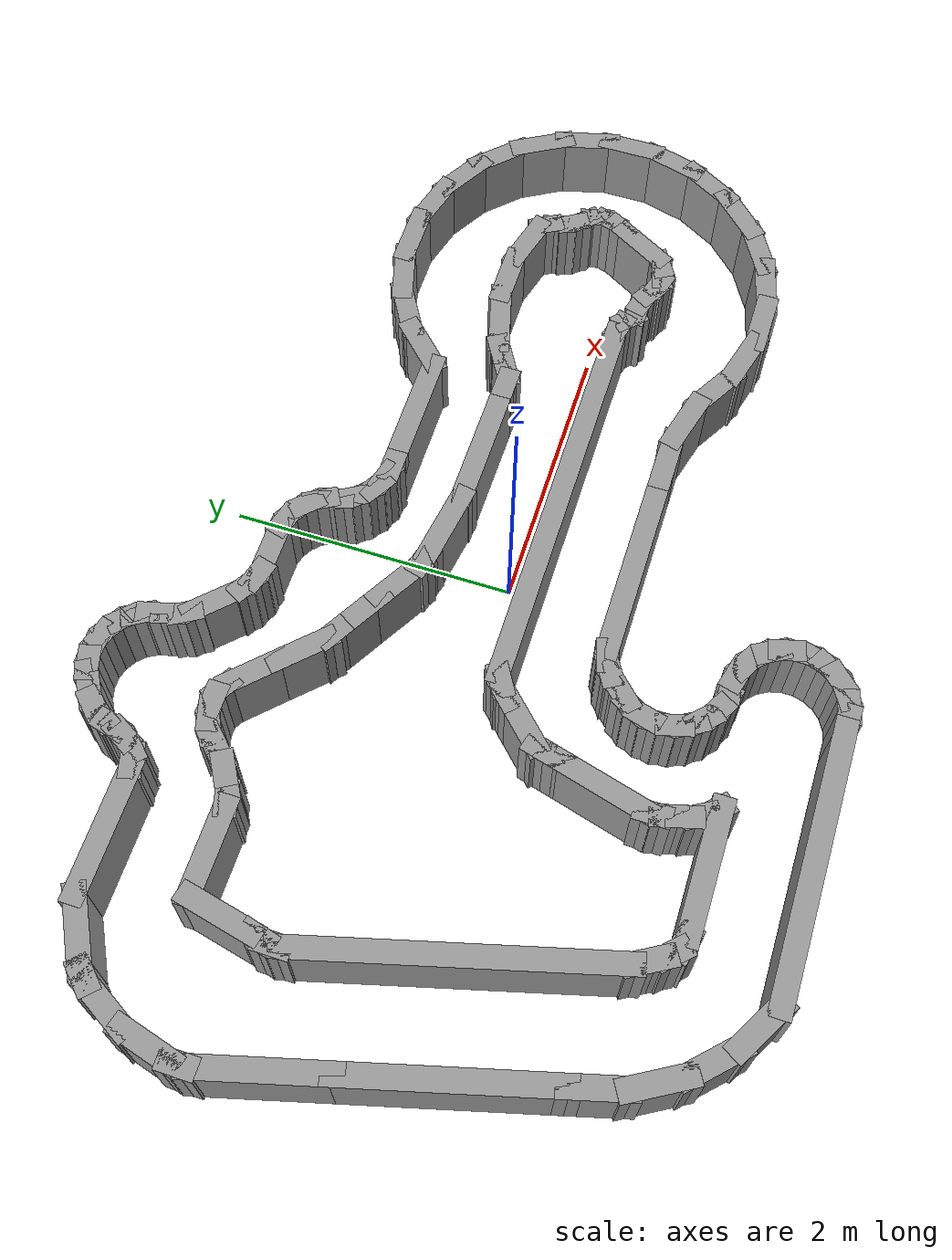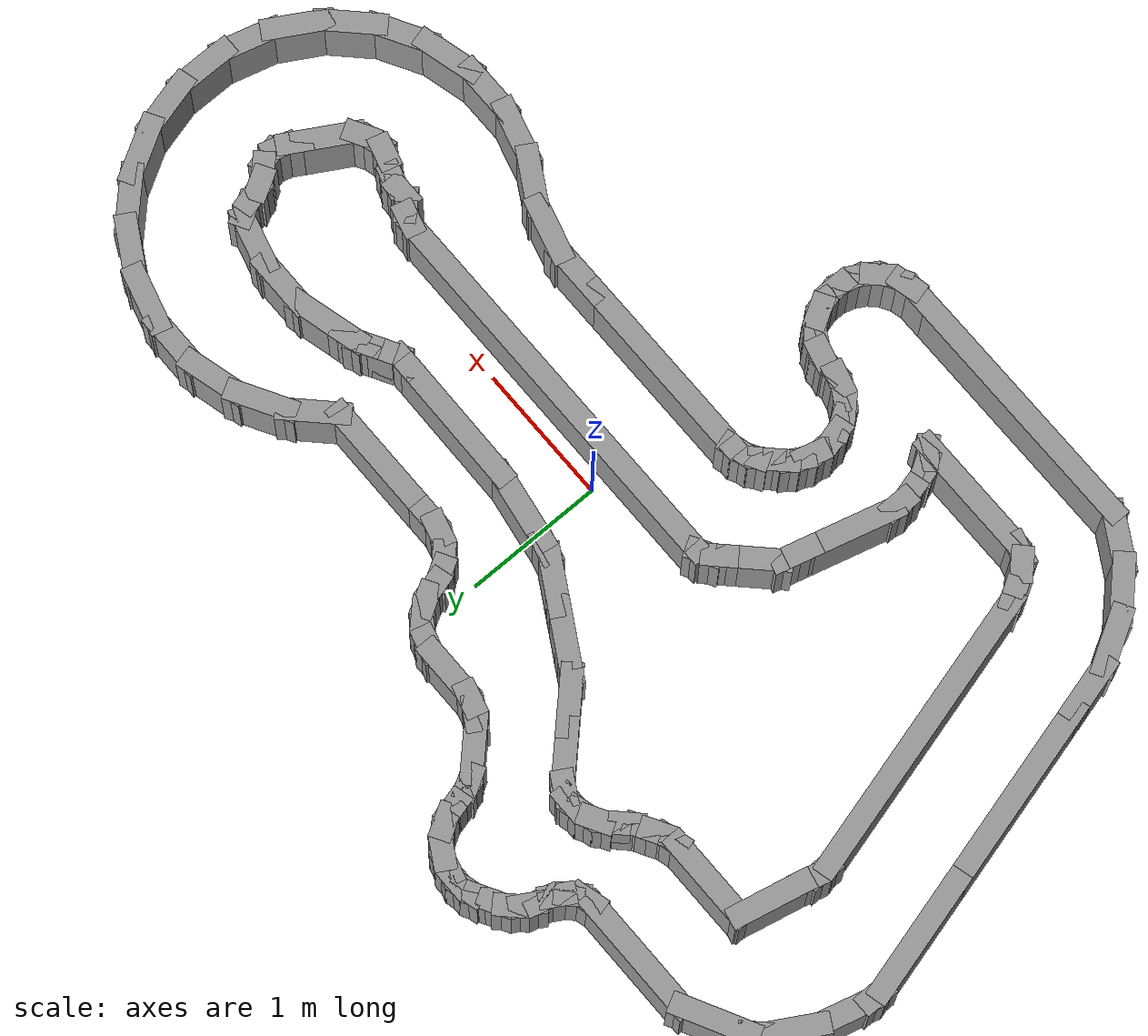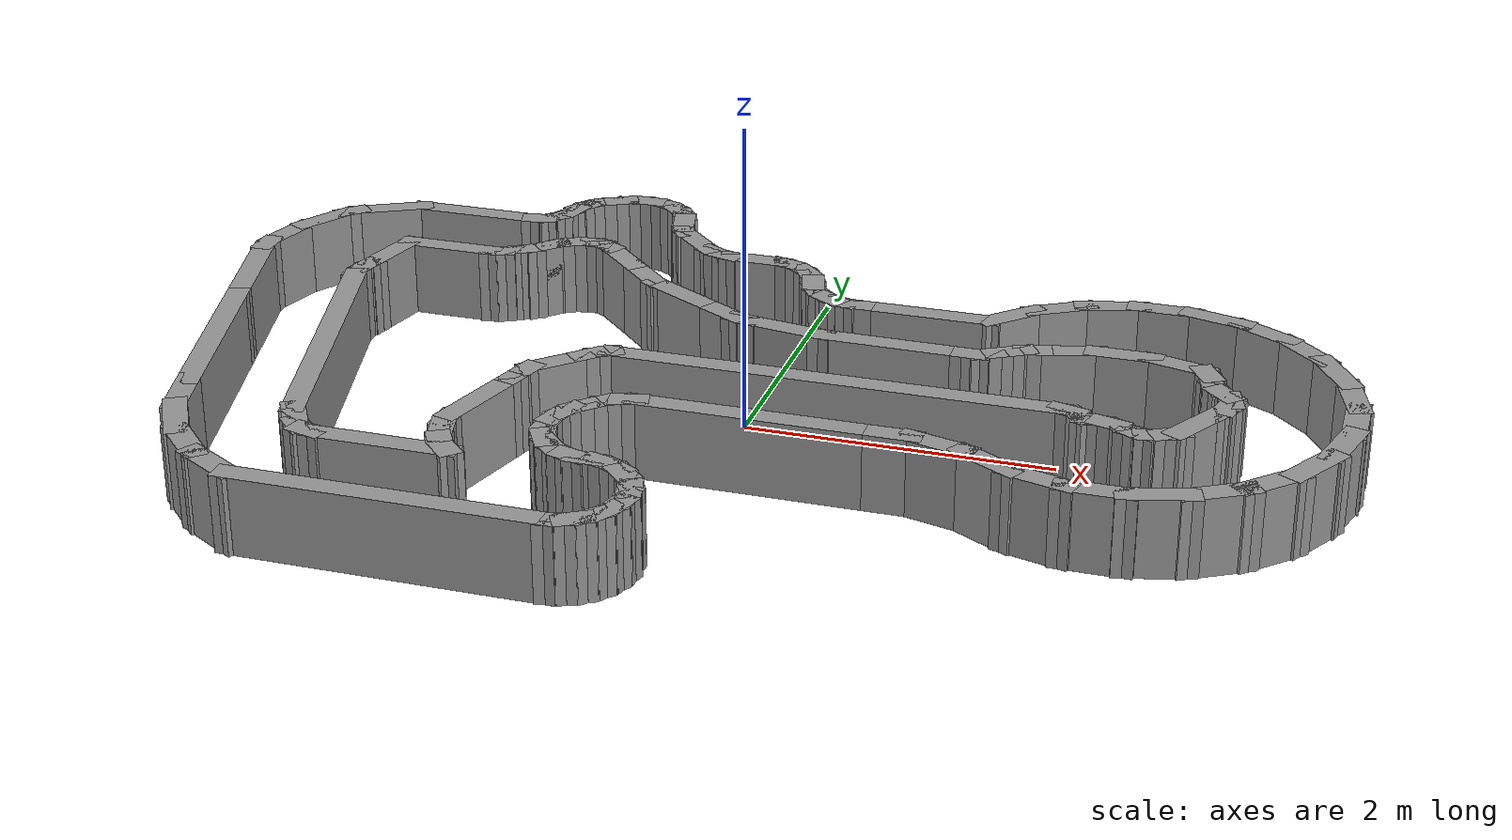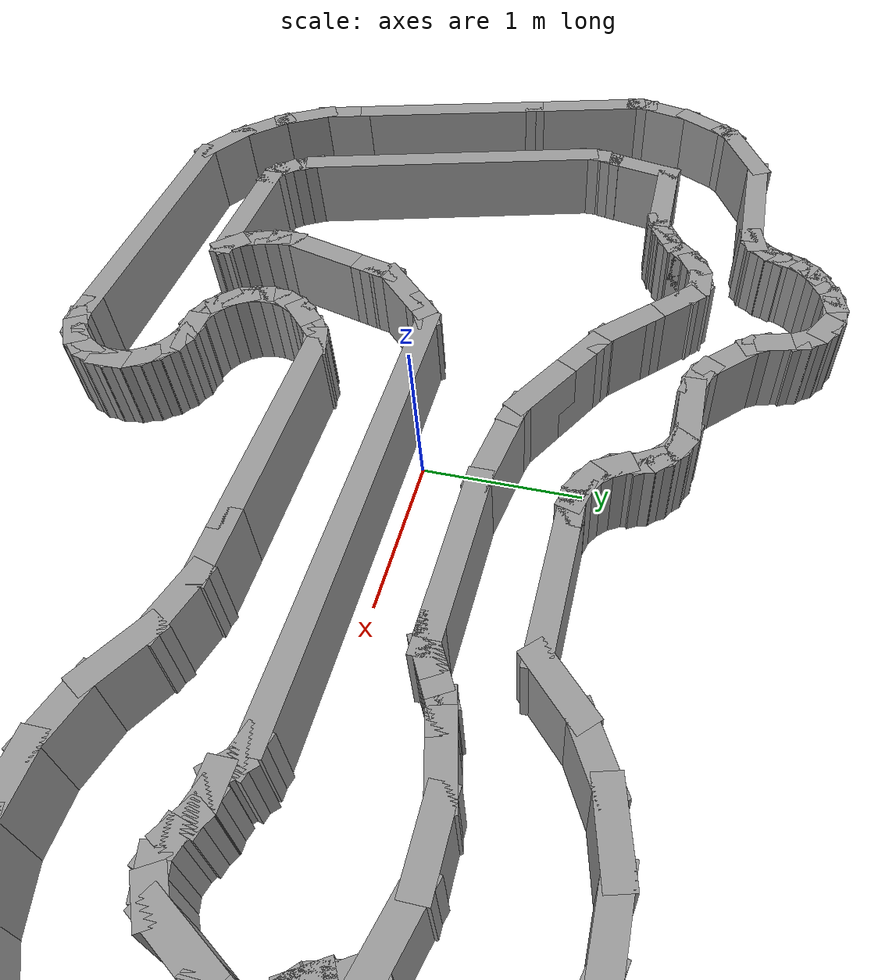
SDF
<?xml version='1.0'?>
<sdf version='1.6'>
  <model name='small_track1'>
    <pose frame=''>0 0 0 0 -0 0</pose>
    <link name='Wall_0'>
      <collision name='Wall_0_Collision'>
        <geometry>
          <box>
            <size>1 0.15 0.5</size>
          </box>
        </geometry>
        <pose frame=''>0 0 0.25 0 -0 0</pose>
      </collision>
      <visual name='Wall_0_Visual'>
        <pose frame=''>0 0 0.25 0 -0 0</pose>
        <geometry>
          <box>
            <size>1 0.15 0.5</size>
          </box>
        </geometry>
        <material>
          <script>
            <uri>file://media/materials/scripts/gazebo.material</uri>
            <name>Gazebo/Grey</name>
          </script>
          <ambient>1 1 1 1</ambient>
        </material>
        <meta>
          <layer>0</layer>
        </meta>
      </visual>
      <pose frame=''>-2.57703 1.83121 0 0 -0 0</pose>
    </link>
    <link name='Wall_1'>
      <collision name='Wall_1_Collision'>
        <geometry>
          <box>
            <size>0.25 0.15 0.5</size>
          </box>
        </geometry>
        <pose frame=''>0 0 0.25 0 -0 0</pose>
      </collision>
      <visual name='Wall_1_Visual'>
        <pose frame=''>0 0 0.25 0 -0 0</pose>
        <geometry>
          <box>
            <size>0.25 0.15 0.5</size>
          </box>
        </geometry>
        <material>
          <script>
            <uri>file://media/materials/scripts/gazebo.material</uri>
            <name>Gazebo/Grey</name>
          </script>
          <ambient>1 1 1 1</ambient>
        </material>
        <meta>
          <layer>0</layer>
        </meta>
      </visual>
      <pose frame=''>-2.10353 1.84421 0 0 -0 0.261885</pose>
    </link>
    <link name='Wall_10'>
      <collision name='Wall_10_Collision'>
        <geometry>
          <box>
            <size>0.25 0.15 0.5</size>
          </box>
        </geometry>
        <pose frame=''>0 0 0.25 0 -0 0</pose>
      </collision>
      <visual name='Wall_10_Visual'>
        <pose frame=''>0 0 0.25 0 -0 0</pose>
        <geometry>
          <box>
            <size>0.25 0.15 0.5</size>
          </box>
        </geometry>
        <material>
          <script>
            <uri>file://media/materials/scripts/gazebo.material</uri>
            <name>Gazebo/Grey</name>
          </script>
          <ambient>1 1 1 1</ambient>
        </material>
        <meta>
          <layer>0</layer>
        </meta>
      </visual>
      <pose frame=''>-1.46803 2.39421 0 0 -0 0</pose>
    </link>
    <link name='Wall_100'>
      <collision name='Wall_100_Collision'>
        <geometry>
          <box>
            <size>0.25 0.15 0.5</size>
          </box>
        </geometry>
        <pose frame=''>0 0 0.25 0 -0 0</pose>
      </collision>
      <visual name='Wall_100_Visual'>
        <pose frame=''>0 0 0.25 0 -0 0</pose>
        <geometry>
          <box>
            <size>0.25 0.15 0.5</size>
          </box>
        </geometry>
        <material>
          <script>
            <uri>file://media/materials/scripts/gazebo.material</uri>
            <name>Gazebo/Grey</name>
          </script>
          <ambient>1 1 1 1</ambient>
        </material>
        <meta>
          <layer>0</layer>
        </meta>
      </visual>
      <pose frame=''>-1.55803 1.51421 0 0 -0 0</pose>
    </link>
    <link name='Wall_101'>
      <collision name='Wall_101_Collision'>
        <geometry>
          <box>
            <size>0.25 0.15 0.5</size>
          </box>
        </geometry>
        <pose frame=''>0 0 0.25 0 -0 0</pose>
      </collision>
      <visual name='Wall_101_Visual'>
        <pose frame=''>0 0 0.25 0 -0 0</pose>
        <geometry>
          <box>
            <size>0.25 0.15 0.5</size>
          </box>
        </geometry>
        <material>
          <script>
            <uri>file://media/materials/scripts/gazebo.material</uri>
            <name>Gazebo/Grey</name>
          </script>
          <ambient>1 1 1 1</ambient>
        </material>
        <meta>
          <layer>0</layer>
        </meta>
      </visual>
      <pose frame=''>-1.46453 1.48921 0 0 -0 -0.521618</pose>
    </link>
    <link name='Wall_102'>
      <collision name='Wall_102_Collision'>
        <geometry>
          <box>
            <size>0.5 0.15 0.5</size>
          </box>
        </geometry>
        <pose frame=''>0 0 0.25 0 -0 0</pose>
      </collision>
      <visual name='Wall_102_Visual'>
        <pose frame=''>0 0 0.25 0 -0 0</pose>
        <geometry>
          <box>
            <size>0.5 0.15 0.5</size>
          </box>
        </geometry>
        <material>
          <script>
            <uri>file://media/materials/scripts/gazebo.material</uri>
            <name>Gazebo/Grey</name>
          </script>
          <ambient>1 1 1 1</ambient>
        </material>
        <meta>
          <layer>0</layer>
        </meta>
      </visual>
      <pose frame=''>-1.29703 1.34071 0 0 -0 -0.783378</pose>
    </link>
    <link name='Wall_103'>
      <collision name='Wall_103_Collision'>
        <geometry>
          <box>
            <size>0.5 0.15 0.5</size>
          </box>
        </geometry>
        <pose frame=''>0 0 0.25 0 -0 0</pose>
      </collision>
      <visual name='Wall_103_Visual'>
        <pose frame=''>0 0 0.25 0 -0 0</pose>
        <geometry>
          <box>
            <size>0.5 0.15 0.5</size>
          </box>
        </geometry>
        <material>
          <script>
            <uri>file://media/materials/scripts/gazebo.material</uri>
            <name>Gazebo/Grey</name>
          </script>
          <ambient>1 1 1 1</ambient>
        </material>
        <meta>
          <layer>0</layer>
        </meta>
      </visual>
      <pose frame=''>-1.04953 1.09321 0 0 -0 -0.787418</pose>
    </link>
    <link name='Wall_104'>
      <collision name='Wall_104_Collision'>
        <geometry>
          <box>
            <size>0.25 0.15 0.5</size>
          </box>
        </geometry>
        <pose frame=''>0 0 0.25 0 -0 0</pose>
      </collision>
      <visual name='Wall_104_Visual'>
        <pose frame=''>0 0 0.25 0 -0 0</pose>
        <geometry>
          <box>
            <size>0.25 0.15 0.5</size>
          </box>
        </geometry>
        <material>
          <script>
            <uri>file://media/materials/scripts/gazebo.material</uri>
            <name>Gazebo/Grey</name>
          </script>
          <ambient>1 1 1 1</ambient>
        </material>
        <meta>
          <layer>0</layer>
        </meta>
      </visual>
      <pose frame=''>-0.882527 0.944206 0 0 -0 -0.521618</pose>
    </link>
    <link name='Wall_105'>
      <collision name='Wall_105_Collision'>
        <geometry>
          <box>
            <size>0.5 0.15 0.5</size>
          </box>
        </geometry>
        <pose frame=''>0 0 0.25 0 -0 0</pose>
      </collision>
      <visual name='Wall_105_Visual'>
        <pose frame=''>0 0 0.25 0 -0 0</pose>
        <geometry>
          <box>
            <size>0.5 0.15 0.5</size>
          </box>
        </geometry>
        <material>
          <script>
            <uri>file://media/materials/scripts/gazebo.material</uri>
            <name>Gazebo/Grey</name>
          </script>
          <ambient>1 1 1 1</ambient>
        </material>
        <meta>
          <layer>0</layer>
        </meta>
      </visual>
      <pose frame=''>-0.687526 0.831706 0 0 -0 -0.523754</pose>
    </link>
    <link name='Wall_106'>
      <collision name='Wall_106_Collision'>
        <geometry>
          <box>
            <size>0.5 0.15 0.5</size>
          </box>
        </geometry>
        <pose frame=''>0 0 0.25 0 -0 0</pose>
      </collision>
      <visual name='Wall_106_Visual'>
        <pose frame=''>0 0 0.25 0 -0 0</pose>
        <geometry>
          <box>
            <size>0.5 0.15 0.5</size>
          </box>
        </geometry>
        <material>
          <script>
            <uri>file://media/materials/scripts/gazebo.material</uri>
            <name>Gazebo/Grey</name>
          </script>
          <ambient>1 1 1 1</ambient>
        </material>
        <meta>
          <layer>0</layer>
        </meta>
      </visual>
      <pose frame=''>-0.384526 0.656706 0 0 -0 -0.523754</pose>
    </link>
    <link name='Wall_11'>
      <collision name='Wall_11_Collision'>
        <geometry>
          <box>
            <size>0.25 0.15 0.5</size>
          </box>
        </geometry>
        <pose frame=''>0 0 0.25 0 -0 0</pose>
      </collision>
      <visual name='Wall_11_Visual'>
        <pose frame=''>0 0 0.25 0 -0 0</pose>
        <geometry>
          <box>
            <size>0.25 0.15 0.5</size>
          </box>
        </geometry>
        <material>
          <script>
            <uri>file://media/materials/scripts/gazebo.material</uri>
            <name>Gazebo/Grey</name>
          </script>
          <ambient>1 1 1 1</ambient>
        </material>
        <meta>
          <layer>0</layer>
        </meta>
      </visual>
      <pose frame=''>-1.37003 2.38121 0 0 -0 -0.264488</pose>
    </link>
    <link name='Wall_112'>
      <collision name='Wall_112_Collision'>
        <geometry>
          <box>
            <size>1.08021 0.15 0.5</size>
          </box>
        </geometry>
        <pose frame=''>0 0 0.25 0 -0 0</pose>
      </collision>
      <visual name='Wall_112_Visual'>
        <pose frame=''>0 0 0.25 0 -0 0</pose>
        <geometry>
          <box>
            <size>1.08021 0.15 0.5</size>
          </box>
        </geometry>
        <material>
          <script>
            <uri>file://media/materials/scripts/gazebo.material</uri>
            <name>Gazebo/Grey</name>
          </script>
          <ambient>1 1 1 1</ambient>
        </material>
        <meta>
          <layer>0</layer>
        </meta>
      </visual>
      <pose frame=''>0.835974 0.458206 0 0 -0 -0.010752</pose>
    </link>
    <link name='Wall_113'>
      <collision name='Wall_113_Collision'>
        <geometry>
          <box>
            <size>0.25 0.15 0.5</size>
          </box>
        </geometry>
        <pose frame=''>0 0 0.25 0 -0 0</pose>
      </collision>
      <visual name='Wall_113_Visual'>
        <pose frame=''>0 0 0.25 0 -0 0</pose>
        <geometry>
          <box>
            <size>0.25 0.15 0.5</size>
          </box>
        </geometry>
        <material>
          <script>
            <uri>file://media/materials/scripts/gazebo.material</uri>
            <name>Gazebo/Grey</name>
          </script>
          <ambient>1 1 1 1</ambient>
        </material>
        <meta>
          <layer>0</layer>
        </meta>
      </visual>
      <pose frame=''>1.35097 0.453206 0 0 -0 0</pose>
    </link>
    <link name='Wall_114'>
      <collision name='Wall_114_Collision'>
        <geometry>
          <box>
            <size>0.25 0.15 0.5</size>
          </box>
        </geometry>
        <pose frame=''>0 0 0.25 0 -0 0</pose>
      </collision>
      <visual name='Wall_114_Visual'>
        <pose frame=''>0 0 0.25 0 -0 0</pose>
        <geometry>
          <box>
            <size>0.25 0.15 0.5</size>
          </box>
        </geometry>
        <material>
          <script>
            <uri>file://media/materials/scripts/gazebo.material</uri>
            <name>Gazebo/Grey</name>
          </script>
          <ambient>1 1 1 1</ambient>
        </material>
        <meta>
          <layer>0</layer>
        </meta>
      </visual>
      <pose frame=''>1.44447 0.478206 0 0 -0 0.521618</pose>
    </link>
    <link name='Wall_115'>
      <collision name='Wall_115_Collision'>
        <geometry>
          <box>
            <size>0.25 0.15 0.5</size>
          </box>
        </geometry>
        <pose frame=''>0 0 0.25 0 -0 0</pose>
      </collision>
      <visual name='Wall_115_Visual'>
        <pose frame=''>0 0 0.25 0 -0 0</pose>
        <geometry>
          <box>
            <size>0.25 0.15 0.5</size>
          </box>
        </geometry>
        <material>
          <script>
            <uri>file://media/materials/scripts/gazebo.material</uri>
            <name>Gazebo/Grey</name>
          </script>
          <ambient>1 1 1 1</ambient>
        </material>
        <meta>
          <layer>0</layer>
        </meta>
      </visual>
      <pose frame=''>1.53147 0.528206 0 0 -0 0.521618</pose>
    </link>
    <link name='Wall_116'>
      <collision name='Wall_116_Collision'>
        <geometry>
          <box>
            <size>0.25 0.15 0.5</size>
          </box>
        </geometry>
        <pose frame=''>0 0 0.25 0 -0 0</pose>
      </collision>
      <visual name='Wall_116_Visual'>
        <pose frame=''>0 0 0.25 0 -0 0</pose>
        <geometry>
          <box>
            <size>0.25 0.15 0.5</size>
          </box>
        </geometry>
        <material>
          <script>
            <uri>file://media/materials/scripts/gazebo.material</uri>
            <name>Gazebo/Grey</name>
          </script>
          <ambient>1 1 1 1</ambient>
        </material>
        <meta>
          <layer>0</layer>
        </meta>
      </visual>
      <pose frame=''>1.61797 0.578206 0 0 -0 0.526627</pose>
    </link>
    <link name='Wall_117'>
      <collision name='Wall_117_Collision'>
        <geometry>
          <box>
            <size>0.25 0.15 0.5</size>
          </box>
        </geometry>
        <pose frame=''>0 0 0.25 0 -0 0</pose>
      </collision>
      <visual name='Wall_117_Visual'>
        <pose frame=''>0 0 0.25 0 -0 0</pose>
        <geometry>
          <box>
            <size>0.25 0.15 0.5</size>
          </box>
        </geometry>
        <material>
          <script>
            <uri>file://media/materials/scripts/gazebo.material</uri>
            <name>Gazebo/Grey</name>
          </script>
          <ambient>1 1 1 1</ambient>
        </material>
        <meta>
          <layer>0</layer>
        </meta>
      </visual>
      <pose frame=''>1.70947 0.616206 0 0 -0 0.261885</pose>
    </link>
    <link name='Wall_118'>
      <collision name='Wall_118_Collision'>
        <geometry>
          <box>
            <size>0.5 0.15 0.5</size>
          </box>
        </geometry>
        <pose frame=''>0 0 0.25 0 -0 0</pose>
      </collision>
      <visual name='Wall_118_Visual'>
        <pose frame=''>0 0 0.25 0 -0 0</pose>
        <geometry>
          <box>
            <size>0.5 0.15 0.5</size>
          </box>
        </geometry>
        <material>
          <script>
            <uri>file://media/materials/scripts/gazebo.material</uri>
            <name>Gazebo/Grey</name>
          </script>
          <ambient>1 1 1 1</ambient>
        </material>
        <meta>
          <layer>0</layer>
        </meta>
      </visual>
      <pose frame=''>1.92697 0.674206 0 0 -0 0.260234</pose>
    </link>
    <link name='Wall_119'>
      <collision name='Wall_119_Collision'>
        <geometry>
          <box>
            <size>0.5 0.15 0.5</size>
          </box>
        </geometry>
        <pose frame=''>0 0 0.25 0 -0 0</pose>
      </collision>
      <visual name='Wall_119_Visual'>
        <pose frame=''>0 0 0.25 0 -0 0</pose>
        <geometry>
          <box>
            <size>0.5 0.15 0.5</size>
          </box>
        </geometry>
        <material>
          <script>
            <uri>file://media/materials/scripts/gazebo.material</uri>
            <name>Gazebo/Grey</name>
          </script>
          <ambient>1 1 1 1</ambient>
        </material>
        <meta>
          <layer>0</layer>
        </meta>
      </visual>
      <pose frame=''>2.27097 0.719206 0 0 -0 0</pose>
    </link>
    <link name='Wall_12'>
      <collision name='Wall_12_Collision'>
        <geometry>
          <box>
            <size>0.25 0.15 0.5</size>
          </box>
        </geometry>
        <pose frame=''>0 0 0.25 0 -0 0</pose>
      </collision>
      <visual name='Wall_12_Visual'>
        <pose frame=''>0 0 0.25 0 -0 0</pose>
        <geometry>
          <box>
            <size>0.25 0.15 0.5</size>
          </box>
        </geometry>
        <material>
          <script>
            <uri>file://media/materials/scripts/gazebo.material</uri>
            <name>Gazebo/Grey</name>
          </script>
          <ambient>1 1 1 1</ambient>
        </material>
        <meta>
          <layer>0</layer>
        </meta>
      </visual>
      <pose frame=''>-1.27853 2.34321 0 0 -0 -0.521618</pose>
    </link>
    <link name='Wall_120'>
      <collision name='Wall_120_Collision'>
        <geometry>
          <box>
            <size>0.5 0.15 0.5</size>
          </box>
        </geometry>
        <pose frame=''>0 0 0.25 0 -0 0</pose>
      </collision>
      <visual name='Wall_120_Visual'>
        <pose frame=''>0 0 0.25 0 -0 0</pose>
        <geometry>
          <box>
            <size>0.5 0.15 0.5</size>
          </box>
        </geometry>
        <material>
          <script>
            <uri>file://media/materials/scripts/gazebo.material</uri>
            <name>Gazebo/Grey</name>
          </script>
          <ambient>1 1 1 1</ambient>
        </material>
        <meta>
          <layer>0</layer>
        </meta>
      </visual>
      <pose frame=''>2.61497 0.674206 0 0 -0 -0.260234</pose>
    </link>
    <link name='Wall_121'>
      <collision name='Wall_121_Collision'>
        <geometry>
          <box>
            <size>0.25 0.15 0.5</size>
          </box>
        </geometry>
        <pose frame=''>0 0 0.25 0 -0 0</pose>
      </collision>
      <visual name='Wall_121_Visual'>
        <pose frame=''>0 0 0.25 0 -0 0</pose>
        <geometry>
          <box>
            <size>0.25 0.15 0.5</size>
          </box>
        </geometry>
        <material>
          <script>
            <uri>file://media/materials/scripts/gazebo.material</uri>
            <name>Gazebo/Grey</name>
          </script>
          <ambient>1 1 1 1</ambient>
        </material>
        <meta>
          <layer>0</layer>
        </meta>
      </visual>
      <pose frame=''>2.80897 0.585706 0 0 -0 -1.04918</pose>
    </link>
    <link name='Wall_122'>
      <collision name='Wall_122_Collision'>
        <geometry>
          <box>
            <size>0.25 0.15 0.5</size>
          </box>
        </geometry>
        <pose frame=''>0 0 0.25 0 -0 0</pose>
      </collision>
      <visual name='Wall_122_Visual'>
        <pose frame=''>0 0 0.25 0 -0 0</pose>
        <geometry>
          <box>
            <size>0.25 0.15 0.5</size>
          </box>
        </geometry>
        <material>
          <script>
            <uri>file://media/materials/scripts/gazebo.material</uri>
            <name>Gazebo/Grey</name>
          </script>
          <ambient>1 1 1 1</ambient>
        </material>
        <meta>
          <layer>0</layer>
        </meta>
      </visual>
      <pose frame=''>2.84697 0.493706 0 0 -0 -1.30891</pose>
    </link>
    <link name='Wall_123'>
      <collision name='Wall_123_Collision'>
        <geometry>
          <box>
            <size>0.25 0.15 0.5</size>
          </box>
        </geometry>
        <pose frame=''>0 0 0.25 0 -0 0</pose>
      </collision>
      <visual name='Wall_123_Visual'>
        <pose frame=''>0 0 0.25 0 -0 0</pose>
        <geometry>
          <box>
            <size>0.25 0.15 0.5</size>
          </box>
        </geometry>
        <material>
          <script>
            <uri>file://media/materials/scripts/gazebo.material</uri>
            <name>Gazebo/Grey</name>
          </script>
          <ambient>1 1 1 1</ambient>
        </material>
        <meta>
          <layer>0</layer>
        </meta>
      </visual>
      <pose frame=''>2.88497 0.402206 0 0 -0 -1.04417</pose>
    </link>
    <link name='Wall_124'>
      <collision name='Wall_124_Collision'>
        <geometry>
          <box>
            <size>0.25 0.15 0.5</size>
          </box>
        </geometry>
        <pose frame=''>0 0 0.25 0 -0 0</pose>
      </collision>
      <visual name='Wall_124_Visual'>
        <pose frame=''>0 0 0.25 0 -0 0</pose>
        <geometry>
          <box>
            <size>0.25 0.15 0.5</size>
          </box>
        </geometry>
        <material>
          <script>
            <uri>file://media/materials/scripts/gazebo.material</uri>
            <name>Gazebo/Grey</name>
          </script>
          <ambient>1 1 1 1</ambient>
        </material>
        <meta>
          <layer>0</layer>
        </meta>
      </visual>
      <pose frame=''>2.94547 0.323706 0 0 -0 -0.785398</pose>
    </link>
    <link name='Wall_125'>
      <collision name='Wall_125_Collision'>
        <geometry>
          <box>
            <size>0.25 0.15 0.5</size>
          </box>
        </geometry>
        <pose frame=''>0 0 0.25 0 -0 0</pose>
      </collision>
      <visual name='Wall_125_Visual'>
        <pose frame=''>0 0 0.25 0 -0 0</pose>
        <geometry>
          <box>
            <size>0.25 0.15 0.5</size>
          </box>
        </geometry>
        <material>
          <script>
            <uri>file://media/materials/scripts/gazebo.material</uri>
            <name>Gazebo/Grey</name>
          </script>
          <ambient>1 1 1 1</ambient>
        </material>
        <meta>
          <layer>0</layer>
        </meta>
      </visual>
      <pose frame=''>2.99397 0.240206 0 0 -0 -1.30631</pose>
    </link>
    <link name='Wall_126'>
      <collision name='Wall_126_Collision'>
        <geometry>
          <box>
            <size>0.25 0.15 0.5</size>
          </box>
        </geometry>
        <pose frame=''>0 0 0.25 0 -0 0</pose>
      </collision>
      <visual name='Wall_126_Visual'>
        <pose frame=''>0 0 0.25 0 -0 0</pose>
        <geometry>
          <box>
            <size>0.25 0.15 0.5</size>
          </box>
        </geometry>
        <material>
          <script>
            <uri>file://media/materials/scripts/gazebo.material</uri>
            <name>Gazebo/Grey</name>
          </script>
          <ambient>1 1 1 1</ambient>
        </material>
        <meta>
          <layer>0</layer>
        </meta>
      </visual>
      <pose frame=''>2.99397 0.143706 0 0 -0 -1.83268</pose>
    </link>
    <link name='Wall_127'>
      <collision name='Wall_127_Collision'>
        <geometry>
          <box>
            <size>0.25 0.15 0.5</size>
          </box>
        </geometry>
        <pose frame=''>0 0 0.25 0 -0 0</pose>
      </collision>
      <visual name='Wall_127_Visual'>
        <pose frame=''>0 0 0.25 0 -0 0</pose>
        <geometry>
          <box>
            <size>0.25 0.15 0.5</size>
          </box>
        </geometry>
        <material>
          <script>
            <uri>file://media/materials/scripts/gazebo.material</uri>
            <name>Gazebo/Grey</name>
          </script>
          <ambient>1 1 1 1</ambient>
        </material>
        <meta>
          <layer>0</layer>
        </meta>
      </visual>
      <pose frame=''>2.95597 0.051706 0 0 -0 -2.09241</pose>
    </link>
    <link name='Wall_128'>
      <collision name='Wall_128_Collision'>
        <geometry>
          <box>
            <size>0.5 0.15 0.5</size>
          </box>
        </geometry>
        <pose frame=''>0 0 0.25 0 -0 0</pose>
      </collision>
      <visual name='Wall_128_Visual'>
        <pose frame=''>0 0 0.25 0 -0 0</pose>
        <geometry>
          <box>
            <size>0.5 0.15 0.5</size>
          </box>
        </geometry>
        <material>
          <script>
            <uri>file://media/materials/scripts/gazebo.material</uri>
            <name>Gazebo/Grey</name>
          </script>
          <ambient>1 1 1 1</ambient>
        </material>
        <meta>
          <layer>0</layer>
        </meta>
      </visual>
      <pose frame=''>2.84347 -0.143294 0 0 -0 -2.09455</pose>
    </link>
    <link name='Wall_129'>
      <collision name='Wall_129_Collision'>
        <geometry>
          <box>
            <size>0.25 0.15 0.5</size>
          </box>
        </geometry>
        <pose frame=''>0 0 0.25 0 -0 0</pose>
      </collision>
      <visual name='Wall_129_Visual'>
        <pose frame=''>0 0 0.25 0 -0 0</pose>
        <geometry>
          <box>
            <size>0.25 0.15 0.5</size>
          </box>
        </geometry>
        <material>
          <script>
            <uri>file://media/materials/scripts/gazebo.material</uri>
            <name>Gazebo/Grey</name>
          </script>
          <ambient>1 1 1 1</ambient>
        </material>
        <meta>
          <layer>0</layer>
        </meta>
      </visual>
      <pose frame=''>2.71247 -0.319794 0 0 -0 -2.61997</pose>
    </link>
    <link name='Wall_13'>
      <collision name='Wall_13_Collision'>
        <geometry>
          <box>
            <size>0.25 0.15 0.5</size>
          </box>
        </geometry>
        <pose frame=''>0 0 0.25 0 -0 0</pose>
      </collision>
      <visual name='Wall_13_Visual'>
        <pose frame=''>0 0 0.25 0 -0 0</pose>
        <geometry>
          <box>
            <size>0.25 0.15 0.5</size>
          </box>
        </geometry>
        <material>
          <script>
            <uri>file://media/materials/scripts/gazebo.material</uri>
            <name>Gazebo/Grey</name>
          </script>
          <ambient>1 1 1 1</ambient>
        </material>
        <meta>
          <layer>0</layer>
        </meta>
      </visual>
      <pose frame=''>-1.19953 2.28271 0 0 -0 -0.785398</pose>
    </link>
    <link name='Wall_130'>
      <collision name='Wall_130_Collision'>
        <geometry>
          <box>
            <size>0.25 0.15 0.5</size>
          </box>
        </geometry>
        <pose frame=''>0 0 0.25 0 -0 0</pose>
      </collision>
      <visual name='Wall_130_Visual'>
        <pose frame=''>0 0 0.25 0 -0 0</pose>
        <geometry>
          <box>
            <size>0.25 0.15 0.5</size>
          </box>
        </geometry>
        <material>
          <script>
            <uri>file://media/materials/scripts/gazebo.material</uri>
            <name>Gazebo/Grey</name>
          </script>
          <ambient>1 1 1 1</ambient>
        </material>
        <meta>
          <layer>0</layer>
        </meta>
      </visual>
      <pose frame=''>2.62047 -0.357794 0 0 -0 -2.87971</pose>
    </link>
    <link name='Wall_131'>
      <collision name='Wall_131_Collision'>
        <geometry>
          <box>
            <size>0.25 0.15 0.5</size>
          </box>
        </geometry>
        <pose frame=''>0 0 0.25 0 -0 0</pose>
      </collision>
      <visual name='Wall_131_Visual'>
        <pose frame=''>0 0 0.25 0 -0 0</pose>
        <geometry>
          <box>
            <size>0.25 0.15 0.5</size>
          </box>
        </geometry>
        <material>
          <script>
            <uri>file://media/materials/scripts/gazebo.material</uri>
            <name>Gazebo/Grey</name>
          </script>
          <ambient>1 1 1 1</ambient>
        </material>
        <meta>
          <layer>0</layer>
        </meta>
      </visual>
      <pose frame=''>2.52397 -0.357794 0 0 -0 2.8771</pose>
    </link>
    <link name='Wall_132'>
      <collision name='Wall_132_Collision'>
        <geometry>
          <box>
            <size>0.25 0.15 0.5</size>
          </box>
        </geometry>
        <pose frame=''>0 0 0.25 0 -0 0</pose>
      </collision>
      <visual name='Wall_132_Visual'>
        <pose frame=''>0 0 0.25 0 -0 0</pose>
        <geometry>
          <box>
            <size>0.25 0.15 0.5</size>
          </box>
        </geometry>
        <material>
          <script>
            <uri>file://media/materials/scripts/gazebo.material</uri>
            <name>Gazebo/Grey</name>
          </script>
          <ambient>1 1 1 1</ambient>
        </material>
        <meta>
          <layer>0</layer>
        </meta>
      </visual>
      <pose frame=''>2.43247 -0.319794 0 0 -0 2.61997</pose>
    </link>
    <link name='Wall_133'>
      <collision name='Wall_133_Collision'>
        <geometry>
          <box>
            <size>0.25 0.15 0.5</size>
          </box>
        </geometry>
        <pose frame=''>0 0 0.25 0 -0 0</pose>
      </collision>
      <visual name='Wall_133_Visual'>
        <pose frame=''>0 0 0.25 0 -0 0</pose>
        <geometry>
          <box>
            <size>0.25 0.15 0.5</size>
          </box>
        </geometry>
        <material>
          <script>
            <uri>file://media/materials/scripts/gazebo.material</uri>
            <name>Gazebo/Grey</name>
          </script>
          <ambient>1 1 1 1</ambient>
        </material>
        <meta>
          <layer>0</layer>
        </meta>
      </visual>
      <pose frame=''>2.34097 -0.281794 0 0 -0 2.8771</pose>
    </link>
    <link name='Wall_134'>
      <collision name='Wall_134_Collision'>
        <geometry>
          <box>
            <size>0.25 0.15 0.5</size>
          </box>
        </geometry>
        <pose frame=''>0 0 0.25 0 -0 0</pose>
      </collision>
      <visual name='Wall_134_Visual'>
        <pose frame=''>0 0 0.25 0 -0 0</pose>
        <geometry>
          <box>
            <size>0.25 0.15 0.5</size>
          </box>
        </geometry>
        <material>
          <script>
            <uri>file://media/materials/scripts/gazebo.material</uri>
            <name>Gazebo/Grey</name>
          </script>
          <ambient>1 1 1 1</ambient>
        </material>
        <meta>
          <layer>0</layer>
        </meta>
      </visual>
      <pose frame=''>2.24297 -0.268794 0 0 -0 3.14159</pose>
    </link>
    <link name='Wall_135'>
      <collision name='Wall_135_Collision'>
        <geometry>
          <box>
            <size>0.25 0.15 0.5</size>
          </box>
        </geometry>
        <pose frame=''>0 0 0.25 0 -0 0</pose>
      </collision>
      <visual name='Wall_135_Visual'>
        <pose frame=''>0 0 0.25 0 -0 0</pose>
        <geometry>
          <box>
            <size>0.25 0.15 0.5</size>
          </box>
        </geometry>
        <material>
          <script>
            <uri>file://media/materials/scripts/gazebo.material</uri>
            <name>Gazebo/Grey</name>
          </script>
          <ambient>1 1 1 1</ambient>
        </material>
        <meta>
          <layer>0</layer>
        </meta>
      </visual>
      <pose frame=''>2.15747 -0.233294 0 0 -0 2.35619</pose>
    </link>
    <link name='Wall_136'>
      <collision name='Wall_136_Collision'>
        <geometry>
          <box>
            <size>0.25 0.15 0.5</size>
          </box>
        </geometry>
        <pose frame=''>0 0 0.25 0 -0 0</pose>
      </collision>
      <visual name='Wall_136_Visual'>
        <pose frame=''>0 0 0.25 0 -0 0</pose>
        <geometry>
          <box>
            <size>0.25 0.15 0.5</size>
          </box>
        </geometry>
        <material>
          <script>
            <uri>file://media/materials/scripts/gazebo.material</uri>
            <name>Gazebo/Grey</name>
          </script>
          <ambient>1 1 1 1</ambient>
        </material>
        <meta>
          <layer>0</layer>
        </meta>
      </visual>
      <pose frame=''>2.07347 -0.184794 0 0 -0 2.87971</pose>
    </link>
    <link name='Wall_137'>
      <collision name='Wall_137_Collision'>
        <geometry>
          <box>
            <size>3 0.15 0.5</size>
          </box>
        </geometry>
        <pose frame=''>0 0 0.25 0 -0 0</pose>
      </collision>
      <visual name='Wall_137_Visual'>
        <pose frame=''>0 0 0.25 0 -0 0</pose>
        <geometry>
          <box>
            <size>3 0.15 0.5</size>
          </box>
        </geometry>
        <material>
          <script>
            <uri>file://media/materials/scripts/gazebo.material</uri>
            <name>Gazebo/Grey</name>
          </script>
          <ambient>1 1 1 1</ambient>
        </material>
        <meta>
          <layer>0</layer>
        </meta>
      </visual>
      <pose frame=''>0.599973 -0.171794 0 0 -0 3.14159</pose>
    </link>
    <link name='Wall_138'>
      <collision name='Wall_138_Collision'>
        <geometry>
          <box>
            <size>0.25 0.15 0.5</size>
          </box>
        </geometry>
        <pose frame=''>0 0 0.25 0 -0 0</pose>
      </collision>
      <visual name='Wall_138_Visual'>
        <pose frame=''>0 0 0.25 0 -0 0</pose>
        <geometry>
          <box>
            <size>0.25 0.15 0.5</size>
          </box>
        </geometry>
        <material>
          <script>
            <uri>file://media/materials/scripts/gazebo.material</uri>
            <name>Gazebo/Grey</name>
          </script>
          <ambient>1 1 1 1</ambient>
        </material>
        <meta>
          <layer>0</layer>
        </meta>
      </visual>
      <pose frame=''>-0.868026 -0.196794 0 0 -0 -2.61497</pose>
    </link>
    <link name='Wall_139'>
      <collision name='Wall_139_Collision'>
        <geometry>
          <box>
            <size>0.25 0.15 0.5</size>
          </box>
        </geometry>
        <pose frame=''>0 0 0.25 0 -0 0</pose>
      </collision>
      <visual name='Wall_139_Visual'>
        <pose frame=''>0 0 0.25 0 -0 0</pose>
        <geometry>
          <box>
            <size>0.25 0.15 0.5</size>
          </box>
        </geometry>
        <material>
          <script>
            <uri>file://media/materials/scripts/gazebo.material</uri>
            <name>Gazebo/Grey</name>
          </script>
          <ambient>1 1 1 1</ambient>
        </material>
        <meta>
          <layer>0</layer>
        </meta>
      </visual>
      <pose frame=''>-0.946526 -0.257294 0 0 -0 -2.35619</pose>
    </link>
    <link name='Wall_14'>
      <collision name='Wall_14_Collision'>
        <geometry>
          <box>
            <size>0.25 0.15 0.5</size>
          </box>
        </geometry>
        <pose frame=''>0 0 0.25 0 -0 0</pose>
      </collision>
      <visual name='Wall_14_Visual'>
        <pose frame=''>0 0 0.25 0 -0 0</pose>
        <geometry>
          <box>
            <size>0.25 0.15 0.5</size>
          </box>
        </geometry>
        <material>
          <script>
            <uri>file://media/materials/scripts/gazebo.material</uri>
            <name>Gazebo/Grey</name>
          </script>
          <ambient>1 1 1 1</ambient>
        </material>
        <meta>
          <layer>0</layer>
        </meta>
      </visual>
      <pose frame=''>-1.13903 2.20421 0 0 -0 -1.04417</pose>
    </link>
    <link name='Wall_140'>
      <collision name='Wall_140_Collision'>
        <geometry>
          <box>
            <size>0.5 0.15 0.5</size>
          </box>
        </geometry>
        <pose frame=''>0 0 0.25 0 -0 0</pose>
      </collision>
      <visual name='Wall_140_Visual'>
        <pose frame=''>0 0 0.25 0 -0 0</pose>
        <geometry>
          <box>
            <size>0.5 0.15 0.5</size>
          </box>
        </geometry>
        <material>
          <script>
            <uri>file://media/materials/scripts/gazebo.material</uri>
            <name>Gazebo/Grey</name>
          </script>
          <ambient>1 1 1 1</ambient>
        </material>
        <meta>
          <layer>0</layer>
        </meta>
      </visual>
      <pose frame=''>-1.10553 -0.416794 0 0 -0 -2.35417</pose>
    </link>
    <link name='Wall_141'>
      <collision name='Wall_141_Collision'>
        <geometry>
          <box>
            <size>0.25 0.15 0.5</size>
          </box>
        </geometry>
        <pose frame=''>0 0 0.25 0 -0 0</pose>
      </collision>
      <visual name='Wall_141_Visual'>
        <pose frame=''>0 0 0.25 0 -0 0</pose>
        <geometry>
          <box>
            <size>0.25 0.15 0.5</size>
          </box>
        </geometry>
        <material>
          <script>
            <uri>file://media/materials/scripts/gazebo.material</uri>
            <name>Gazebo/Grey</name>
          </script>
          <ambient>1 1 1 1</ambient>
        </material>
        <meta>
          <layer>0</layer>
        </meta>
      </visual>
      <pose frame=''>-1.24203 -0.588794 0 0 -0 -1.83529</pose>
    </link>
    <link name='Wall_142'>
      <collision name='Wall_142_Collision'>
        <geometry>
          <box>
            <size>0.25 0.15 0.5</size>
          </box>
        </geometry>
        <pose frame=''>0 0 0.25 0 -0 0</pose>
      </collision>
      <visual name='Wall_142_Visual'>
        <pose frame=''>0 0 0.25 0 -0 0</pose>
        <geometry>
          <box>
            <size>0.25 0.15 0.5</size>
          </box>
        </geometry>
        <material>
          <script>
            <uri>file://media/materials/scripts/gazebo.material</uri>
            <name>Gazebo/Grey</name>
          </script>
          <ambient>1 1 1 1</ambient>
        </material>
        <meta>
          <layer>0</layer>
        </meta>
      </visual>
      <pose frame=''>-1.26803 -0.685294 0 0 -0 -1.83268</pose>
    </link>
    <link name='Wall_143'>
      <collision name='Wall_143_Collision'>
        <geometry>
          <box>
            <size>0.75 0.15 0.5</size>
          </box>
        </geometry>
        <pose frame=''>0 0 0.25 0 -0 0</pose>
      </collision>
      <visual name='Wall_143_Visual'>
        <pose frame=''>0 0 0.25 0 -0 0</pose>
        <geometry>
          <box>
            <size>0.75 0.15 0.5</size>
          </box>
        </geometry>
        <material>
          <script>
            <uri>file://media/materials/scripts/gazebo.material</uri>
            <name>Gazebo/Grey</name>
          </script>
          <ambient>1 1 1 1</ambient>
        </material>
        <meta>
          <layer>0</layer>
        </meta>
      </visual>
      <pose frame=''>-1.35903 -1.0233 0 0 -0 -1.83398</pose>
    </link>
    <link name='Wall_144'>
      <collision name='Wall_144_Collision'>
        <geometry>
          <box>
            <size>0.25 0.15 0.5</size>
          </box>
        </geometry>
        <pose frame=''>0 0 0.25 0 -0 0</pose>
      </collision>
      <visual name='Wall_144_Visual'>
        <pose frame=''>0 0 0.25 0 -0 0</pose>
        <geometry>
          <box>
            <size>0.25 0.15 0.5</size>
          </box>
        </geometry>
        <material>
          <script>
            <uri>file://media/materials/scripts/gazebo.material</uri>
            <name>Gazebo/Grey</name>
          </script>
          <ambient>1 1 1 1</ambient>
        </material>
        <meta>
          <layer>0</layer>
        </meta>
      </visual>
      <pose frame=''>-1.43703 -1.36279 0 0 -0 -1.5708</pose>
    </link>
    <link name='Wall_145'>
      <collision name='Wall_145_Collision'>
        <geometry>
          <box>
            <size>0.25 0.15 0.5</size>
          </box>
        </geometry>
        <pose frame=''>0 0 0.25 0 -0 0</pose>
      </collision>
      <visual name='Wall_145_Visual'>
        <pose frame=''>0 0 0.25 0 -0 0</pose>
        <geometry>
          <box>
            <size>0.25 0.15 0.5</size>
          </box>
        </geometry>
        <material>
          <script>
            <uri>file://media/materials/scripts/gazebo.material</uri>
            <name>Gazebo/Grey</name>
          </script>
          <ambient>1 1 1 1</ambient>
        </material>
        <meta>
          <layer>0</layer>
        </meta>
      </visual>
      <pose frame=''>-1.42403 -1.46129 0 0 -0 -1.30891</pose>
    </link>
    <link name='Wall_146'>
      <collision name='Wall_146_Collision'>
        <geometry>
          <box>
            <size>0.25 0.15 0.5</size>
          </box>
        </geometry>
        <pose frame=''>0 0 0.25 0 -0 0</pose>
      </collision>
      <visual name='Wall_146_Visual'>
        <pose frame=''>0 0 0.25 0 -0 0</pose>
        <geometry>
          <box>
            <size>0.25 0.15 0.5</size>
          </box>
        </geometry>
        <material>
          <script>
            <uri>file://media/materials/scripts/gazebo.material</uri>
            <name>Gazebo/Grey</name>
          </script>
          <ambient>1 1 1 1</ambient>
        </material>
        <meta>
          <layer>0</layer>
        </meta>
      </visual>
      <pose frame=''>-1.39803 -1.55779 0 0 -0 -1.30631</pose>
    </link>
    <link name='Wall_147'>
      <collision name='Wall_147_Collision'>
        <geometry>
          <box>
            <size>0.25 0.15 0.5</size>
          </box>
        </geometry>
        <pose frame=''>0 0 0.25 0 -0 0</pose>
      </collision>
      <visual name='Wall_147_Visual'>
        <pose frame=''>0 0 0.25 0 -0 0</pose>
        <geometry>
          <box>
            <size>0.25 0.15 0.5</size>
          </box>
        </geometry>
        <material>
          <script>
            <uri>file://media/materials/scripts/gazebo.material</uri>
            <name>Gazebo/Grey</name>
          </script>
          <ambient>1 1 1 1</ambient>
        </material>
        <meta>
          <layer>0</layer>
        </meta>
      </visual>
      <pose frame=''>-1.36003 -1.64929 0 0 -0 -1.04918</pose>
    </link>
    <link name='Wall_148'>
      <collision name='Wall_148_Collision'>
        <geometry>
          <box>
            <size>0.25 0.15 0.5</size>
          </box>
        </geometry>
        <pose frame=''>0 0 0.25 0 -0 0</pose>
      </collision>
      <visual name='Wall_148_Visual'>
        <pose frame=''>0 0 0.25 0 -0 0</pose>
        <geometry>
          <box>
            <size>0.25 0.15 0.5</size>
          </box>
        </geometry>
        <material>
          <script>
            <uri>file://media/materials/scripts/gazebo.material</uri>
            <name>Gazebo/Grey</name>
          </script>
          <ambient>1 1 1 1</ambient>
        </material>
        <meta>
          <layer>0</layer>
        </meta>
      </visual>
      <pose frame=''>-1.29953 -1.72829 0 0 -0 -0.785398</pose>
    </link>
    <link name='Wall_149'>
      <collision name='Wall_149_Collision'>
        <geometry>
          <box>
            <size>1 0.15 0.5</size>
          </box>
        </geometry>
        <pose frame=''>0 0 0.25 0 -0 0</pose>
      </collision>
      <visual name='Wall_149_Visual'>
        <pose frame=''>0 0 0.25 0 -0 0</pose>
        <geometry>
          <box>
            <size>1 0.15 0.5</size>
          </box>
        </geometry>
        <material>
          <script>
            <uri>file://media/materials/scripts/gazebo.material</uri>
            <name>Gazebo/Grey</name>
          </script>
          <ambient>1 1 1 1</ambient>
        </material>
        <meta>
          <layer>0</layer>
        </meta>
      </visual>
      <pose frame=''>-1.68903 -1.76379 0 0 -0 3.14159</pose>
    </link>
    <link name='Wall_15'>
      <collision name='Wall_15_Collision'>
        <geometry>
          <box>
            <size>0.25 0.15 0.5</size>
          </box>
        </geometry>
        <pose frame=''>0 0 0.25 0 -0 0</pose>
      </collision>
      <visual name='Wall_15_Visual'>
        <pose frame=''>0 0 0.25 0 -0 0</pose>
        <geometry>
          <box>
            <size>0.25 0.15 0.5</size>
          </box>
        </geometry>
        <material>
          <script>
            <uri>file://media/materials/scripts/gazebo.material</uri>
            <name>Gazebo/Grey</name>
          </script>
          <ambient>1 1 1 1</ambient>
        </material>
        <meta>
          <layer>0</layer>
        </meta>
      </visual>
      <pose frame=''>-1.10153 2.11271 0 0 -0 -1.31855</pose>
    </link>
    <link name='Wall_150'>
      <collision name='Wall_150_Collision'>
        <geometry>
          <box>
            <size>0.25 0.15 0.5</size>
          </box>
        </geometry>
        <pose frame=''>0 0 0.25 0 -0 0</pose>
      </collision>
      <visual name='Wall_150_Visual'>
        <pose frame=''>0 0 0.25 0 -0 0</pose>
        <geometry>
          <box>
            <size>0.25 0.15 0.5</size>
          </box>
        </geometry>
        <material>
          <script>
            <uri>file://media/materials/scripts/gazebo.material</uri>
            <name>Gazebo/Grey</name>
          </script>
          <ambient>1 1 1 1</ambient>
        </material>
        <meta>
          <layer>0</layer>
        </meta>
      </visual>
      <pose frame=''>-2.16253 -1.75079 0 0 -0 2.87971</pose>
    </link>
    <link name='Wall_151'>
      <collision name='Wall_151_Collision'>
        <geometry>
          <box>
            <size>0.25 0.15 0.5</size>
          </box>
        </geometry>
        <pose frame=''>0 0 0.25 0 -0 0</pose>
      </collision>
      <visual name='Wall_151_Visual'>
        <pose frame=''>0 0 0.25 0 -0 0</pose>
        <geometry>
          <box>
            <size>0.25 0.15 0.5</size>
          </box>
        </geometry>
        <material>
          <script>
            <uri>file://media/materials/scripts/gazebo.material</uri>
            <name>Gazebo/Grey</name>
          </script>
          <ambient>1 1 1 1</ambient>
        </material>
        <meta>
          <layer>0</layer>
        </meta>
      </visual>
      <pose frame=''>-2.24603 -1.70229 0 0 -0 2.3491</pose>
    </link>
    <link name='Wall_152'>
      <collision name='Wall_152_Collision'>
        <geometry>
          <box>
            <size>0.25 0.15 0.5</size>
          </box>
        </geometry>
        <pose frame=''>0 0 0.25 0 -0 0</pose>
      </collision>
      <visual name='Wall_152_Visual'>
        <pose frame=''>0 0 0.25 0 -0 0</pose>
        <geometry>
          <box>
            <size>0.25 0.15 0.5</size>
          </box>
        </geometry>
        <material>
          <script>
            <uri>file://media/materials/scripts/gazebo.material</uri>
            <name>Gazebo/Grey</name>
          </script>
          <ambient>1 1 1 1</ambient>
        </material>
        <meta>
          <layer>0</layer>
        </meta>
      </visual>
      <pose frame=''>-2.30603 -1.62379 0 0 -0 2.09742</pose>
    </link>
    <link name='Wall_153'>
      <collision name='Wall_153_Collision'>
        <geometry>
          <box>
            <size>0.25 0.15 0.5</size>
          </box>
        </geometry>
        <pose frame=''>0 0 0.25 0 -0 0</pose>
      </collision>
      <visual name='Wall_153_Visual'>
        <pose frame=''>0 0 0.25 0 -0 0</pose>
        <geometry>
          <box>
            <size>0.25 0.15 0.5</size>
          </box>
        </geometry>
        <material>
          <script>
            <uri>file://media/materials/scripts/gazebo.material</uri>
            <name>Gazebo/Grey</name>
          </script>
          <ambient>1 1 1 1</ambient>
        </material>
        <meta>
          <layer>0</layer>
        </meta>
      </visual>
      <pose frame=''>-2.35603 -1.53729 0 0 -0 2.09241</pose>
    </link>
    <link name='Wall_154'>
      <collision name='Wall_154_Collision'>
        <geometry>
          <box>
            <size>2.25 0.15 0.5</size>
          </box>
        </geometry>
        <pose frame=''>0 0 0.25 0 -0 0</pose>
      </collision>
      <visual name='Wall_154_Visual'>
        <pose frame=''>0 0 0.25 0 -0 0</pose>
        <geometry>
          <box>
            <size>2.25 0.15 0.5</size>
          </box>
        </geometry>
        <material>
          <script>
            <uri>file://media/materials/scripts/gazebo.material</uri>
            <name>Gazebo/Grey</name>
          </script>
          <ambient>1 1 1 1</ambient>
        </material>
        <meta>
          <layer>0</layer>
        </meta>
      </visual>
      <pose frame=''>-2.65303 -0.479794 0 0 -0 1.83287</pose>
    </link>
    <link name='Wall_155'>
      <collision name='Wall_155_Collision'>
        <geometry>
          <box>
            <size>0.25 0.15 0.5</size>
          </box>
        </geometry>
        <pose frame=''>0 0 0.25 0 -0 0</pose>
      </collision>
      <visual name='Wall_155_Visual'>
        <pose frame=''>0 0 0.25 0 -0 0</pose>
        <geometry>
          <box>
            <size>0.25 0.15 0.5</size>
          </box>
        </geometry>
        <material>
          <script>
            <uri>file://media/materials/scripts/gazebo.material</uri>
            <name>Gazebo/Grey</name>
          </script>
          <ambient>1 1 1 1</ambient>
        </material>
        <meta>
          <layer>0</layer>
        </meta>
      </visual>
      <pose frame=''>-2.92503 0.584206 0 0 -0 1.5708</pose>
    </link>
    <link name='Wall_156'>
      <collision name='Wall_156_Collision'>
        <geometry>
          <box>
            <size>0.25 0.15 0.5</size>
          </box>
        </geometry>
        <pose frame=''>0 0 0.25 0 -0 0</pose>
      </collision>
      <visual name='Wall_156_Visual'>
        <pose frame=''>0 0 0.25 0 -0 0</pose>
        <geometry>
          <box>
            <size>0.25 0.15 0.5</size>
          </box>
        </geometry>
        <material>
          <script>
            <uri>file://media/materials/scripts/gazebo.material</uri>
            <name>Gazebo/Grey</name>
          </script>
          <ambient>1 1 1 1</ambient>
        </material>
        <meta>
          <layer>0</layer>
        </meta>
      </visual>
      <pose frame=''>-2.91203 0.682706 0 0 -0 1.30891</pose>
    </link>
    <link name='Wall_157'>
      <collision name='Wall_157_Collision'>
        <geometry>
          <box>
            <size>0.600474 0.15 0.5</size>
          </box>
        </geometry>
        <pose frame=''>0 0 0.25 0 -0 0</pose>
      </collision>
      <visual name='Wall_157_Visual'>
        <pose frame=''>0 0 0.25 0 -0 0</pose>
        <geometry>
          <box>
            <size>0.600474 0.15 0.5</size>
          </box>
        </geometry>
        <material>
          <script>
            <uri>file://media/materials/scripts/gazebo.material</uri>
            <name>Gazebo/Grey</name>
          </script>
          <ambient>1 1 1 1</ambient>
        </material>
        <meta>
          <layer>0</layer>
        </meta>
      </visual>
      <pose frame=''>-2.85053 0.951206 0 0 -0 1.35381</pose>
    </link>
    <link name='Wall_159'>
      <collision name='Wall_159_Collision'>
        <geometry>
          <box>
            <size>0.25 0.15 0.5</size>
          </box>
        </geometry>
        <pose frame=''>0 0 0.25 0 -0 0</pose>
      </collision>
      <visual name='Wall_159_Visual'>
        <pose frame=''>0 0 0.25 0 -0 0</pose>
        <geometry>
          <box>
            <size>0.25 0.15 0.5</size>
          </box>
        </geometry>
        <material>
          <script>
            <uri>file://media/materials/scripts/gazebo.material</uri>
            <name>Gazebo/Grey</name>
          </script>
          <ambient>1 1 1 1</ambient>
        </material>
        <meta>
          <layer>0</layer>
        </meta>
      </visual>
      <pose frame=''>-0.184526 0.556206 0 0 -0 -0.261885</pose>
    </link>
    <link name='Wall_16'>
      <collision name='Wall_16_Collision'>
        <geometry>
          <box>
            <size>0.25 0.15 0.5</size>
          </box>
        </geometry>
        <pose frame=''>0 0 0.25 0 -0 0</pose>
      </collision>
      <visual name='Wall_16_Visual'>
        <pose frame=''>0 0 0.25 0 -0 0</pose>
        <geometry>
          <box>
            <size>0.25 0.15 0.5</size>
          </box>
        </geometry>
        <material>
          <script>
            <uri>file://media/materials/scripts/gazebo.material</uri>
            <name>Gazebo/Grey</name>
          </script>
          <ambient>1 1 1 1</ambient>
        </material>
        <meta>
          <layer>0</layer>
        </meta>
      </visual>
      <pose frame=''>-1.07603 2.01621 0 0 -0 -1.30631</pose>
    </link>
    <link name='Wall_160'>
      <collision name='Wall_160_Collision'>
        <geometry>
          <box>
            <size>0.663694 0.15 0.5</size>
          </box>
        </geometry>
        <pose frame=''>0 0 0.25 0 -0 0</pose>
      </collision>
      <visual name='Wall_160_Visual'>
        <pose frame=''>0 0 0.25 0 -0 0</pose>
        <geometry>
          <box>
            <size>0.663694 0.15 0.5</size>
          </box>
        </geometry>
        <material>
          <script>
            <uri>file://media/materials/scripts/gazebo.material</uri>
            <name>Gazebo/Grey</name>
          </script>
          <ambient>1 1 1 1</ambient>
        </material>
        <meta>
          <layer>0</layer>
        </meta>
      </visual>
      <pose frame=''>0.117473 0.503206 0 0 -0 -0.156501</pose>
    </link>
    <link name='Wall_17'>
      <collision name='Wall_17_Collision'>
        <geometry>
          <box>
            <size>0.25 0.15 0.5</size>
          </box>
        </geometry>
        <pose frame=''>0 0 0.25 0 -0 0</pose>
      </collision>
      <visual name='Wall_17_Visual'>
        <pose frame=''>0 0 0.25 0 -0 0</pose>
        <geometry>
          <box>
            <size>0.25 0.15 0.5</size>
          </box>
        </geometry>
        <material>
          <script>
            <uri>file://media/materials/scripts/gazebo.material</uri>
            <name>Gazebo/Grey</name>
          </script>
          <ambient>1 1 1 1</ambient>
        </material>
        <meta>
          <layer>0</layer>
        </meta>
      </visual>
      <pose frame=''>-1.03803 1.92471 0 0 -0 -1.04918</pose>
    </link>
    <link name='Wall_18'>
      <collision name='Wall_18_Collision'>
        <geometry>
          <box>
            <size>0.5 0.15 0.5</size>
          </box>
        </geometry>
        <pose frame=''>0 0 0.25 0 -0 0</pose>
      </collision>
      <visual name='Wall_18_Visual'>
        <pose frame=''>0 0 0.25 0 -0 0</pose>
        <geometry>
          <box>
            <size>0.5 0.15 0.5</size>
          </box>
        </geometry>
        <material>
          <script>
            <uri>file://media/materials/scripts/gazebo.material</uri>
            <name>Gazebo/Grey</name>
          </script>
          <ambient>1 1 1 1</ambient>
        </material>
        <meta>
          <layer>0</layer>
        </meta>
      </visual>
      <pose frame=''>-0.889026 1.75771 0 0 -0 -0.783378</pose>
    </link>
    <link name='Wall_19'>
      <collision name='Wall_19_Collision'>
        <geometry>
          <box>
            <size>0.25 0.15 0.5</size>
          </box>
        </geometry>
        <pose frame=''>0 0 0.25 0 -0 0</pose>
      </collision>
      <visual name='Wall_19_Visual'>
        <pose frame=''>0 0 0.25 0 -0 0</pose>
        <geometry>
          <box>
            <size>0.25 0.15 0.5</size>
          </box>
        </geometry>
        <material>
          <script>
            <uri>file://media/materials/scripts/gazebo.material</uri>
            <name>Gazebo/Grey</name>
          </script>
          <ambient>1 1 1 1</ambient>
        </material>
        <meta>
          <layer>0</layer>
        </meta>
      </visual>
      <pose frame=''>-0.722027 1.60921 0 0 -0 -0.526627</pose>
    </link>
    <link name='Wall_2'>
      <collision name='Wall_2_Collision'>
        <geometry>
          <box>
            <size>0.25 0.15 0.5</size>
          </box>
        </geometry>
        <pose frame=''>0 0 0.25 0 -0 0</pose>
      </collision>
      <visual name='Wall_2_Visual'>
        <pose frame=''>0 0 0.25 0 -0 0</pose>
        <geometry>
          <box>
            <size>0.25 0.15 0.5</size>
          </box>
        </geometry>
        <material>
          <script>
            <uri>file://media/materials/scripts/gazebo.material</uri>
            <name>Gazebo/Grey</name>
          </script>
          <ambient>1 1 1 1</ambient>
        </material>
        <meta>
          <layer>0</layer>
        </meta>
      </visual>
      <pose frame=''>-2.02003 1.89271 0 0 -0 0.79249</pose>
    </link>
    <link name='Wall_20'>
      <collision name='Wall_20_Collision'>
        <geometry>
          <box>
            <size>0.25 0.15 0.5</size>
          </box>
        </geometry>
        <pose frame=''>0 0 0.25 0 -0 0</pose>
      </collision>
      <visual name='Wall_20_Visual'>
        <pose frame=''>0 0 0.25 0 -0 0</pose>
        <geometry>
          <box>
            <size>0.25 0.15 0.5</size>
          </box>
        </geometry>
        <material>
          <script>
            <uri>file://media/materials/scripts/gazebo.material</uri>
            <name>Gazebo/Grey</name>
          </script>
          <ambient>1 1 1 1</ambient>
        </material>
        <meta>
          <layer>0</layer>
        </meta>
      </visual>
      <pose frame=''>-0.630526 1.57121 0 0 -0 -0.261885</pose>
    </link>
    <link name='Wall_21'>
      <collision name='Wall_21_Collision'>
        <geometry>
          <box>
            <size>0.5 0.15 0.5</size>
          </box>
        </geometry>
        <pose frame=''>0 0 0.25 0 -0 0</pose>
      </collision>
      <visual name='Wall_21_Visual'>
        <pose frame=''>0 0 0.25 0 -0 0</pose>
        <geometry>
          <box>
            <size>0.5 0.15 0.5</size>
          </box>
        </geometry>
        <material>
          <script>
            <uri>file://media/materials/scripts/gazebo.material</uri>
            <name>Gazebo/Grey</name>
          </script>
          <ambient>1 1 1 1</ambient>
        </material>
        <meta>
          <layer>0</layer>
        </meta>
      </visual>
      <pose frame=''>-0.407027 1.55821 0 0 -0 0</pose>
    </link>
    <link name='Wall_22'>
      <collision name='Wall_22_Collision'>
        <geometry>
          <box>
            <size>0.25 0.15 0.5</size>
          </box>
        </geometry>
        <pose frame=''>0 0 0.25 0 -0 0</pose>
      </collision>
      <visual name='Wall_22_Visual'>
        <pose frame=''>0 0 0.25 0 -0 0</pose>
        <geometry>
          <box>
            <size>0.25 0.15 0.5</size>
          </box>
        </geometry>
        <material>
          <script>
            <uri>file://media/materials/scripts/gazebo.material</uri>
            <name>Gazebo/Grey</name>
          </script>
          <ambient>1 1 1 1</ambient>
        </material>
        <meta>
          <layer>0</layer>
        </meta>
      </visual>
      <pose frame=''>-0.183526 1.54521 0 0 -0 -0.261885</pose>
    </link>
    <link name='Wall_23'>
      <collision name='Wall_23_Collision'>
        <geometry>
          <box>
            <size>0.25 0.15 0.5</size>
          </box>
        </geometry>
        <pose frame=''>0 0 0.25 0 -0 0</pose>
      </collision>
      <visual name='Wall_23_Visual'>
        <pose frame=''>0 0 0.25 0 -0 0</pose>
        <geometry>
          <box>
            <size>0.25 0.15 0.5</size>
          </box>
        </geometry>
        <material>
          <script>
            <uri>file://media/materials/scripts/gazebo.material</uri>
            <name>Gazebo/Grey</name>
          </script>
          <ambient>1 1 1 1</ambient>
        </material>
        <meta>
          <layer>0</layer>
        </meta>
      </visual>
      <pose frame=''>-0.092026 1.50721 0 0 -0 -0.526627</pose>
    </link>
    <link name='Wall_24'>
      <collision name='Wall_24_Collision'>
        <geometry>
          <box>
            <size>0.25 0.15 0.5</size>
          </box>
        </geometry>
        <pose frame=''>0 0 0.25 0 -0 0</pose>
      </collision>
      <visual name='Wall_24_Visual'>
        <pose frame=''>0 0 0.25 0 -0 0</pose>
        <geometry>
          <box>
            <size>0.25 0.15 0.5</size>
          </box>
        </geometry>
        <material>
          <script>
            <uri>file://media/materials/scripts/gazebo.material</uri>
            <name>Gazebo/Grey</name>
          </script>
          <ambient>1 1 1 1</ambient>
        </material>
        <meta>
          <layer>0</layer>
        </meta>
      </visual>
      <pose frame=''>-0.013526 1.44671 0 0 -0 -0.785398</pose>
    </link>
    <link name='Wall_25'>
      <collision name='Wall_25_Collision'>
        <geometry>
          <box>
            <size>0.25 0.15 0.5</size>
          </box>
        </geometry>
        <pose frame=''>0 0 0.25 0 -0 0</pose>
      </collision>
      <visual name='Wall_25_Visual'>
        <pose frame=''>0 0 0.25 0 -0 0</pose>
        <geometry>
          <box>
            <size>0.25 0.15 0.5</size>
          </box>
        </geometry>
        <material>
          <script>
            <uri>file://media/materials/scripts/gazebo.material</uri>
            <name>Gazebo/Grey</name>
          </script>
          <ambient>1 1 1 1</ambient>
        </material>
        <meta>
          <layer>0</layer>
        </meta>
      </visual>
      <pose frame=''>0.046973 1.36771 0 0 -0 -1.04918</pose>
    </link>
    <link name='Wall_26'>
      <collision name='Wall_26_Collision'>
        <geometry>
          <box>
            <size>0.25 0.15 0.5</size>
          </box>
        </geometry>
        <pose frame=''>0 0 0.25 0 -0 0</pose>
      </collision>
      <visual name='Wall_26_Visual'>
        <pose frame=''>0 0 0.25 0 -0 0</pose>
        <geometry>
          <box>
            <size>0.25 0.15 0.5</size>
          </box>
        </geometry>
        <material>
          <script>
            <uri>file://media/materials/scripts/gazebo.material</uri>
            <name>Gazebo/Grey</name>
          </script>
          <ambient>1 1 1 1</ambient>
        </material>
        <meta>
          <layer>0</layer>
        </meta>
      </visual>
      <pose frame=''>0.084974 1.27621 0 0 -0 -1.30631</pose>
    </link>
    <link name='Wall_27'>
      <collision name='Wall_27_Collision'>
        <geometry>
          <box>
            <size>0.25 0.15 0.5</size>
          </box>
        </geometry>
        <pose frame=''>0 0 0.25 0 -0 0</pose>
      </collision>
      <visual name='Wall_27_Visual'>
        <pose frame=''>0 0 0.25 0 -0 0</pose>
        <geometry>
          <box>
            <size>0.25 0.15 0.5</size>
          </box>
        </geometry>
        <material>
          <script>
            <uri>file://media/materials/scripts/gazebo.material</uri>
            <name>Gazebo/Grey</name>
          </script>
          <ambient>1 1 1 1</ambient>
        </material>
        <meta>
          <layer>0</layer>
        </meta>
      </visual>
      <pose frame=''>0.122974 1.18471 0 0 -0 -1.04918</pose>
    </link>
    <link name='Wall_28'>
      <collision name='Wall_28_Collision'>
        <geometry>
          <box>
            <size>0.25 0.15 0.5</size>
          </box>
        </geometry>
        <pose frame=''>0 0 0.25 0 -0 0</pose>
      </collision>
      <visual name='Wall_28_Visual'>
        <pose frame=''>0 0 0.25 0 -0 0</pose>
        <geometry>
          <box>
            <size>0.25 0.15 0.5</size>
          </box>
        </geometry>
        <material>
          <script>
            <uri>file://media/materials/scripts/gazebo.material</uri>
            <name>Gazebo/Grey</name>
          </script>
          <ambient>1 1 1 1</ambient>
        </material>
        <meta>
          <layer>0</layer>
        </meta>
      </visual>
      <pose frame=''>0.183473 1.10621 0 0 -0 -0.778306</pose>
    </link>
    <link name='Wall_29'>
      <collision name='Wall_29_Collision'>
        <geometry>
          <box>
            <size>0.25 0.15 0.5</size>
          </box>
        </geometry>
        <pose frame=''>0 0 0.25 0 -0 0</pose>
      </collision>
      <visual name='Wall_29_Visual'>
        <pose frame=''>0 0 0.25 0 -0 0</pose>
        <geometry>
          <box>
            <size>0.25 0.15 0.5</size>
          </box>
        </geometry>
        <material>
          <script>
            <uri>file://media/materials/scripts/gazebo.material</uri>
            <name>Gazebo/Grey</name>
          </script>
          <ambient>1 1 1 1</ambient>
        </material>
        <meta>
          <layer>0</layer>
        </meta>
      </visual>
      <pose frame=''>0.261974 1.04621 0 0 -0 -0.526627</pose>
    </link>
    <link name='Wall_3'>
      <collision name='Wall_3_Collision'>
        <geometry>
          <box>
            <size>0.25 0.15 0.5</size>
          </box>
        </geometry>
        <pose frame=''>0 0 0.25 0 -0 0</pose>
      </collision>
      <visual name='Wall_3_Visual'>
        <pose frame=''>0 0 0.25 0 -0 0</pose>
        <geometry>
          <box>
            <size>0.25 0.15 0.5</size>
          </box>
        </geometry>
        <material>
          <script>
            <uri>file://media/materials/scripts/gazebo.material</uri>
            <name>Gazebo/Grey</name>
          </script>
          <ambient>1 1 1 1</ambient>
        </material>
        <meta>
          <layer>0</layer>
        </meta>
      </visual>
      <pose frame=''>-1.96003 1.97121 0 0 -0 1.04417</pose>
    </link>
    <link name='Wall_30'>
      <collision name='Wall_30_Collision'>
        <geometry>
          <box>
            <size>0.25 0.15 0.5</size>
          </box>
        </geometry>
        <pose frame=''>0 0 0.25 0 -0 0</pose>
      </collision>
      <visual name='Wall_30_Visual'>
        <pose frame=''>0 0 0.25 0 -0 0</pose>
        <geometry>
          <box>
            <size>0.25 0.15 0.5</size>
          </box>
        </geometry>
        <material>
          <script>
            <uri>file://media/materials/scripts/gazebo.material</uri>
            <name>Gazebo/Grey</name>
          </script>
          <ambient>1 1 1 1</ambient>
        </material>
        <meta>
          <layer>0</layer>
        </meta>
      </visual>
      <pose frame=''>0.353473 1.00821 0 0 -0 -0.261885</pose>
    </link>
    <link name='Wall_31'>
      <collision name='Wall_31_Collision'>
        <geometry>
          <box>
            <size>0.25 0.15 0.5</size>
          </box>
        </geometry>
        <pose frame=''>0 0 0.25 0 -0 0</pose>
      </collision>
      <visual name='Wall_31_Visual'>
        <pose frame=''>0 0 0.25 0 -0 0</pose>
        <geometry>
          <box>
            <size>0.25 0.15 0.5</size>
          </box>
        </geometry>
        <material>
          <script>
            <uri>file://media/materials/scripts/gazebo.material</uri>
            <name>Gazebo/Grey</name>
          </script>
          <ambient>1 1 1 1</ambient>
        </material>
        <meta>
          <layer>0</layer>
        </meta>
      </visual>
      <pose frame=''>0.451974 0.995206 0 0 -0 0</pose>
    </link>
    <link name='Wall_32'>
      <collision name='Wall_32_Collision'>
        <geometry>
          <box>
            <size>1 0.15 0.5</size>
          </box>
        </geometry>
        <pose frame=''>0 0 0.25 0 -0 0</pose>
      </collision>
      <visual name='Wall_32_Visual'>
        <pose frame=''>0 0 0.25 0 -0 0</pose>
        <geometry>
          <box>
            <size>1 0.15 0.5</size>
          </box>
        </geometry>
        <material>
          <script>
            <uri>file://media/materials/scripts/gazebo.material</uri>
            <name>Gazebo/Grey</name>
          </script>
          <ambient>1 1 1 1</ambient>
        </material>
        <meta>
          <layer>0</layer>
        </meta>
      </visual>
      <pose frame=''>0.926974 0.995206 0 0 -0 0</pose>
    </link>
    <link name='Wall_33'>
      <collision name='Wall_33_Collision'>
        <geometry>
          <box>
            <size>0.5 0.15 0.5</size>
          </box>
        </geometry>
        <pose frame=''>0 0 0.25 0 -0 0</pose>
      </collision>
      <visual name='Wall_33_Visual'>
        <pose frame=''>0 0 0.25 0 -0 0</pose>
        <geometry>
          <box>
            <size>0.5 0.15 0.5</size>
          </box>
        </geometry>
        <material>
          <script>
            <uri>file://media/materials/scripts/gazebo.material</uri>
            <name>Gazebo/Grey</name>
          </script>
          <ambient>1 1 1 1</ambient>
        </material>
        <meta>
          <layer>0</layer>
        </meta>
      </visual>
      <pose frame=''>1.47547 1.11871 0 0 -0 0.785398</pose>
    </link>
    <link name='Wall_34'>
      <collision name='Wall_34_Collision'>
        <geometry>
          <box>
            <size>0.5 0.15 0.5</size>
          </box>
        </geometry>
        <pose frame=''>0 0 0.25 0 -0 0</pose>
      </collision>
      <visual name='Wall_34_Visual'>
        <pose frame=''>0 0 0.25 0 -0 0</pose>
        <geometry>
          <box>
            <size>0.5 0.15 0.5</size>
          </box>
        </geometry>
        <material>
          <script>
            <uri>file://media/materials/scripts/gazebo.material</uri>
            <name>Gazebo/Grey</name>
          </script>
          <ambient>1 1 1 1</ambient>
        </material>
        <meta>
          <layer>0</layer>
        </meta>
      </visual>
      <pose frame=''>1.75047 1.32971 0 0 -0 0.523754</pose>
    </link>
    <link name='Wall_35'>
      <collision name='Wall_35_Collision'>
        <geometry>
          <box>
            <size>0.5 0.15 0.5</size>
          </box>
        </geometry>
        <pose frame=''>0 0 0.25 0 -0 0</pose>
      </collision>
      <visual name='Wall_35_Visual'>
        <pose frame=''>0 0 0.25 0 -0 0</pose>
        <geometry>
          <box>
            <size>0.5 0.15 0.5</size>
          </box>
        </geometry>
        <material>
          <script>
            <uri>file://media/materials/scripts/gazebo.material</uri>
            <name>Gazebo/Grey</name>
          </script>
          <ambient>1 1 1 1</ambient>
        </material>
        <meta>
          <layer>0</layer>
        </meta>
      </visual>
      <pose frame=''>2.07097 1.46271 0 0 -0 0.262995</pose>
    </link>
    <link name='Wall_36'>
      <collision name='Wall_36_Collision'>
        <geometry>
          <box>
            <size>0.5 0.15 0.5</size>
          </box>
        </geometry>
        <pose frame=''>0 0 0.25 0 -0 0</pose>
      </collision>
      <visual name='Wall_36_Visual'>
        <pose frame=''>0 0 0.25 0 -0 0</pose>
        <geometry>
          <box>
            <size>0.5 0.15 0.5</size>
          </box>
        </geometry>
        <material>
          <script>
            <uri>file://media/materials/scripts/gazebo.material</uri>
            <name>Gazebo/Grey</name>
          </script>
          <ambient>1 1 1 1</ambient>
        </material>
        <meta>
          <layer>0</layer>
        </meta>
      </visual>
      <pose frame=''>2.41497 1.50821 0 0 -0 0</pose>
    </link>
    <link name='Wall_37'>
      <collision name='Wall_37_Collision'>
        <geometry>
          <box>
            <size>0.5 0.15 0.5</size>
          </box>
        </geometry>
        <pose frame=''>0 0 0.25 0 -0 0</pose>
      </collision>
      <visual name='Wall_37_Visual'>
        <pose frame=''>0 0 0.25 0 -0 0</pose>
        <geometry>
          <box>
            <size>0.5 0.15 0.5</size>
          </box>
        </geometry>
        <material>
          <script>
            <uri>file://media/materials/scripts/gazebo.material</uri>
            <name>Gazebo/Grey</name>
          </script>
          <ambient>1 1 1 1</ambient>
        </material>
        <meta>
          <layer>0</layer>
        </meta>
      </visual>
      <pose frame=''>2.75897 1.46271 0 0 -0 -0.262995</pose>
    </link>
    <link name='Wall_38'>
      <collision name='Wall_38_Collision'>
        <geometry>
          <box>
            <size>0.5 0.15 0.5</size>
          </box>
        </geometry>
        <pose frame=''>0 0 0.25 0 -0 0</pose>
      </collision>
      <visual name='Wall_38_Visual'>
        <pose frame=''>0 0 0.25 0 -0 0</pose>
        <geometry>
          <box>
            <size>0.5 0.15 0.5</size>
          </box>
        </geometry>
        <material>
          <script>
            <uri>file://media/materials/scripts/gazebo.material</uri>
            <name>Gazebo/Grey</name>
          </script>
          <ambient>1 1 1 1</ambient>
        </material>
        <meta>
          <layer>0</layer>
        </meta>
      </visual>
      <pose frame=''>3.07997 1.32971 0 0 -0 -0.522329</pose>
    </link>
    <link name='Wall_39'>
      <collision name='Wall_39_Collision'>
        <geometry>
          <box>
            <size>0.5 0.15 0.5</size>
          </box>
        </geometry>
        <pose frame=''>0 0 0.25 0 -0 0</pose>
      </collision>
      <visual name='Wall_39_Visual'>
        <pose frame=''>0 0 0.25 0 -0 0</pose>
        <geometry>
          <box>
            <size>0.5 0.15 0.5</size>
          </box>
        </geometry>
        <material>
          <script>
            <uri>file://media/materials/scripts/gazebo.material</uri>
            <name>Gazebo/Grey</name>
          </script>
          <ambient>1 1 1 1</ambient>
        </material>
        <meta>
          <layer>0</layer>
        </meta>
      </visual>
      <pose frame=''>3.35547 1.11871 0 0 -0 -0.785398</pose>
    </link>
    <link name='Wall_4'>
      <collision name='Wall_4_Collision'>
        <geometry>
          <box>
            <size>0.25 0.15 0.5</size>
          </box>
        </geometry>
        <pose frame=''>0 0 0.25 0 -0 0</pose>
      </collision>
      <visual name='Wall_4_Visual'>
        <pose frame=''>0 0 0.25 0 -0 0</pose>
        <geometry>
          <box>
            <size>0.25 0.15 0.5</size>
          </box>
        </geometry>
        <material>
          <script>
            <uri>file://media/materials/scripts/gazebo.material</uri>
            <name>Gazebo/Grey</name>
          </script>
          <ambient>1 1 1 1</ambient>
        </material>
        <meta>
          <layer>0</layer>
        </meta>
      </visual>
      <pose frame=''>-1.92203 2.06271 0 0 -0 1.30891</pose>
    </link>
    <link name='Wall_40'>
      <collision name='Wall_40_Collision'>
        <geometry>
          <box>
            <size>0.5 0.15 0.5</size>
          </box>
        </geometry>
        <pose frame=''>0 0 0.25 0 -0 0</pose>
      </collision>
      <visual name='Wall_40_Visual'>
        <pose frame=''>0 0 0.25 0 -0 0</pose>
        <geometry>
          <box>
            <size>0.5 0.15 0.5</size>
          </box>
        </geometry>
        <material>
          <script>
            <uri>file://media/materials/scripts/gazebo.material</uri>
            <name>Gazebo/Grey</name>
          </script>
          <ambient>1 1 1 1</ambient>
        </material>
        <meta>
          <layer>0</layer>
        </meta>
      </visual>
      <pose frame=''>3.56647 0.843706 0 0 -0 -1.04704</pose>
    </link>
    <link name='Wall_41'>
      <collision name='Wall_41_Collision'>
        <geometry>
          <box>
            <size>0.501001 0.15 0.5</size>
          </box>
        </geometry>
        <pose frame=''>0 0 0.25 0 -0 0</pose>
      </collision>
      <visual name='Wall_41_Visual'>
        <pose frame=''>0 0 0.25 0 -0 0</pose>
        <geometry>
          <box>
            <size>0.501001 0.15 0.5</size>
          </box>
        </geometry>
        <material>
          <script>
            <uri>file://media/materials/scripts/gazebo.material</uri>
            <name>Gazebo/Grey</name>
          </script>
          <ambient>1 1 1 1</ambient>
        </material>
        <meta>
          <layer>0</layer>
        </meta>
      </visual>
      <pose frame=''>3.69947 0.522706 0 0 -0 -1.30854</pose>
    </link>
    <link name='Wall_42'>
      <collision name='Wall_42_Collision'>
        <geometry>
          <box>
            <size>0.5 0.15 0.5</size>
          </box>
        </geometry>
        <pose frame=''>0 0 0.25 0 -0 0</pose>
      </collision>
      <visual name='Wall_42_Visual'>
        <pose frame=''>0 0 0.25 0 -0 0</pose>
        <geometry>
          <box>
            <size>0.5 0.15 0.5</size>
          </box>
        </geometry>
        <material>
          <script>
            <uri>file://media/materials/scripts/gazebo.material</uri>
            <name>Gazebo/Grey</name>
          </script>
          <ambient>1 1 1 1</ambient>
        </material>
        <meta>
          <layer>0</layer>
        </meta>
      </visual>
      <pose frame=''>3.74497 0.178206 0 0 -0 -1.5708</pose>
    </link>
    <link name='Wall_43'>
      <collision name='Wall_43_Collision'>
        <geometry>
          <box>
            <size>0.5 0.15 0.5</size>
          </box>
        </geometry>
        <pose frame=''>0 0 0.25 0 -0 0</pose>
      </collision>
      <visual name='Wall_43_Visual'>
        <pose frame=''>0 0 0.25 0 -0 0</pose>
        <geometry>
          <box>
            <size>0.5 0.15 0.5</size>
          </box>
        </geometry>
        <material>
          <script>
            <uri>file://media/materials/scripts/gazebo.material</uri>
            <name>Gazebo/Grey</name>
          </script>
          <ambient>1 1 1 1</ambient>
        </material>
        <meta>
          <layer>0</layer>
        </meta>
      </visual>
      <pose frame=''>3.69947 -0.165794 0 0 -0 -1.83379</pose>
    </link>
    <link name='Wall_44'>
      <collision name='Wall_44_Collision'>
        <geometry>
          <box>
            <size>0.5 0.15 0.5</size>
          </box>
        </geometry>
        <pose frame=''>0 0 0.25 0 -0 0</pose>
      </collision>
      <visual name='Wall_44_Visual'>
        <pose frame=''>0 0 0.25 0 -0 0</pose>
        <geometry>
          <box>
            <size>0.5 0.15 0.5</size>
          </box>
        </geometry>
        <material>
          <script>
            <uri>file://media/materials/scripts/gazebo.material</uri>
            <name>Gazebo/Grey</name>
          </script>
          <ambient>1 1 1 1</ambient>
        </material>
        <meta>
          <layer>0</layer>
        </meta>
      </visual>
      <pose frame=''>3.56647 -0.486294 0 0 -0 -2.09455</pose>
    </link>
    <link name='Wall_45'>
      <collision name='Wall_45_Collision'>
        <geometry>
          <box>
            <size>0.5 0.15 0.5</size>
          </box>
        </geometry>
        <pose frame=''>0 0 0.25 0 -0 0</pose>
      </collision>
      <visual name='Wall_45_Visual'>
        <pose frame=''>0 0 0.25 0 -0 0</pose>
        <geometry>
          <box>
            <size>0.5 0.15 0.5</size>
          </box>
        </geometry>
        <material>
          <script>
            <uri>file://media/materials/scripts/gazebo.material</uri>
            <name>Gazebo/Grey</name>
          </script>
          <ambient>1 1 1 1</ambient>
        </material>
        <meta>
          <layer>0</layer>
        </meta>
      </visual>
      <pose frame=''>3.35547 -0.761294 0 0 -0 -2.35619</pose>
    </link>
    <link name='Wall_46'>
      <collision name='Wall_46_Collision'>
        <geometry>
          <box>
            <size>0.5 0.15 0.5</size>
          </box>
        </geometry>
        <pose frame=''>0 0 0.25 0 -0 0</pose>
      </collision>
      <visual name='Wall_46_Visual'>
        <pose frame=''>0 0 0.25 0 -0 0</pose>
        <geometry>
          <box>
            <size>0.5 0.15 0.5</size>
          </box>
        </geometry>
        <material>
          <script>
            <uri>file://media/materials/scripts/gazebo.material</uri>
            <name>Gazebo/Grey</name>
          </script>
          <ambient>1 1 1 1</ambient>
        </material>
        <meta>
          <layer>0</layer>
        </meta>
      </visual>
      <pose frame=''>3.07997 -0.972294 0 0 -0 -2.61926</pose>
    </link>
    <link name='Wall_47'>
      <collision name='Wall_47_Collision'>
        <geometry>
          <box>
            <size>0.5 0.15 0.5</size>
          </box>
        </geometry>
        <pose frame=''>0 0 0.25 0 -0 0</pose>
      </collision>
      <visual name='Wall_47_Visual'>
        <pose frame=''>0 0 0.25 0 -0 0</pose>
        <geometry>
          <box>
            <size>0.5 0.15 0.5</size>
          </box>
        </geometry>
        <material>
          <script>
            <uri>file://media/materials/scripts/gazebo.material</uri>
            <name>Gazebo/Grey</name>
          </script>
          <ambient>1 1 1 1</ambient>
        </material>
        <meta>
          <layer>0</layer>
        </meta>
      </visual>
      <pose frame=''>2.75897 -1.10529 0 0 -0 -2.8786</pose>
    </link>
    <link name='Wall_48'>
      <collision name='Wall_48_Collision'>
        <geometry>
          <box>
            <size>0.5 0.15 0.5</size>
          </box>
        </geometry>
        <pose frame=''>0 0 0.25 0 -0 0</pose>
      </collision>
      <visual name='Wall_48_Visual'>
        <pose frame=''>0 0 0.25 0 -0 0</pose>
        <geometry>
          <box>
            <size>0.5 0.15 0.5</size>
          </box>
        </geometry>
        <material>
          <script>
            <uri>file://media/materials/scripts/gazebo.material</uri>
            <name>Gazebo/Grey</name>
          </script>
          <ambient>1 1 1 1</ambient>
        </material>
        <meta>
          <layer>0</layer>
        </meta>
      </visual>
      <pose frame=''>2.41497 -1.15079 0 0 -0 3.14159</pose>
    </link>
    <link name='Wall_49'>
      <collision name='Wall_49_Collision'>
        <geometry>
          <box>
            <size>0.5 0.15 0.5</size>
          </box>
        </geometry>
        <pose frame=''>0 0 0.25 0 -0 0</pose>
      </collision>
      <visual name='Wall_49_Visual'>
        <pose frame=''>0 0 0.25 0 -0 0</pose>
        <geometry>
          <box>
            <size>0.5 0.15 0.5</size>
          </box>
        </geometry>
        <material>
          <script>
            <uri>file://media/materials/scripts/gazebo.material</uri>
            <name>Gazebo/Grey</name>
          </script>
          <ambient>1 1 1 1</ambient>
        </material>
        <meta>
          <layer>0</layer>
        </meta>
      </visual>
      <pose frame=''>2.07097 -1.10529 0 0 -0 2.8786</pose>
    </link>
    <link name='Wall_5'>
      <collision name='Wall_5_Collision'>
        <geometry>
          <box>
            <size>0.25 0.15 0.5</size>
          </box>
        </geometry>
        <pose frame=''>0 0 0.25 0 -0 0</pose>
      </collision>
      <visual name='Wall_5_Visual'>
        <pose frame=''>0 0 0.25 0 -0 0</pose>
        <geometry>
          <box>
            <size>0.25 0.15 0.5</size>
          </box>
        </geometry>
        <material>
          <script>
            <uri>file://media/materials/scripts/gazebo.material</uri>
            <name>Gazebo/Grey</name>
          </script>
          <ambient>1 1 1 1</ambient>
        </material>
        <meta>
          <layer>0</layer>
        </meta>
      </visual>
      <pose frame=''>-1.88403 2.15421 0 0 -0 1.04417</pose>
    </link>
    <link name='Wall_50'>
      <collision name='Wall_50_Collision'>
        <geometry>
          <box>
            <size>0.5 0.15 0.5</size>
          </box>
        </geometry>
        <pose frame=''>0 0 0.25 0 -0 0</pose>
      </collision>
      <visual name='Wall_50_Visual'>
        <pose frame=''>0 0 0.25 0 -0 0</pose>
        <geometry>
          <box>
            <size>0.5 0.15 0.5</size>
          </box>
        </geometry>
        <material>
          <script>
            <uri>file://media/materials/scripts/gazebo.material</uri>
            <name>Gazebo/Grey</name>
          </script>
          <ambient>1 1 1 1</ambient>
        </material>
        <meta>
          <layer>0</layer>
        </meta>
      </visual>
      <pose frame=''>1.75047 -0.972294 0 0 -0 2.61784</pose>
    </link>
    <link name='Wall_51'>
      <collision name='Wall_51_Collision'>
        <geometry>
          <box>
            <size>0.5 0.15 0.5</size>
          </box>
        </geometry>
        <pose frame=''>0 0 0.25 0 -0 0</pose>
      </collision>
      <visual name='Wall_51_Visual'>
        <pose frame=''>0 0 0.25 0 -0 0</pose>
        <geometry>
          <box>
            <size>0.5 0.15 0.5</size>
          </box>
        </geometry>
        <material>
          <script>
            <uri>file://media/materials/scripts/gazebo.material</uri>
            <name>Gazebo/Grey</name>
          </script>
          <ambient>1 1 1 1</ambient>
        </material>
        <meta>
          <layer>0</layer>
        </meta>
      </visual>
      <pose frame=''>1.42997 -0.839794 0 0 -0 2.88136</pose>
    </link>
    <link name='Wall_52'>
      <collision name='Wall_52_Collision'>
        <geometry>
          <box>
            <size>0.5 0.15 0.5</size>
          </box>
        </geometry>
        <pose frame=''>0 0 0.25 0 -0 0</pose>
      </collision>
      <visual name='Wall_52_Visual'>
        <pose frame=''>0 0 0.25 0 -0 0</pose>
        <geometry>
          <box>
            <size>0.5 0.15 0.5</size>
          </box>
        </geometry>
        <material>
          <script>
            <uri>file://media/materials/scripts/gazebo.material</uri>
            <name>Gazebo/Grey</name>
          </script>
          <ambient>1 1 1 1</ambient>
        </material>
        <meta>
          <layer>0</layer>
        </meta>
      </visual>
      <pose frame=''>1.08597 -0.794794 0 0 -0 3.14159</pose>
    </link>
    <link name='Wall_53'>
      <collision name='Wall_53_Collision'>
        <geometry>
          <box>
            <size>1.5 0.15 0.5</size>
          </box>
        </geometry>
        <pose frame=''>0 0 0.25 0 -0 0</pose>
      </collision>
      <visual name='Wall_53_Visual'>
        <pose frame=''>0 0 0.25 0 -0 0</pose>
        <geometry>
          <box>
            <size>1.5 0.15 0.5</size>
          </box>
        </geometry>
        <material>
          <script>
            <uri>file://media/materials/scripts/gazebo.material</uri>
            <name>Gazebo/Grey</name>
          </script>
          <ambient>1 1 1 1</ambient>
        </material>
        <meta>
          <layer>0</layer>
        </meta>
      </visual>
      <pose frame=''>0.235974 -0.794794 0 0 -0 3.14159</pose>
    </link>
    <link name='Wall_54'>
      <collision name='Wall_54_Collision'>
        <geometry>
          <box>
            <size>0.25 0.15 0.5</size>
          </box>
        </geometry>
        <pose frame=''>0 0 0.25 0 -0 0</pose>
      </collision>
      <visual name='Wall_54_Visual'>
        <pose frame=''>0 0 0.25 0 -0 0</pose>
        <geometry>
          <box>
            <size>0.25 0.15 0.5</size>
          </box>
        </geometry>
        <material>
          <script>
            <uri>file://media/materials/scripts/gazebo.material</uri>
            <name>Gazebo/Grey</name>
          </script>
          <ambient>1 1 1 1</ambient>
        </material>
        <meta>
          <layer>0</layer>
        </meta>
      </visual>
      <pose frame=''>-0.487026 -0.807794 0 0 -0 -2.8771</pose>
    </link>
    <link name='Wall_55'>
      <collision name='Wall_55_Collision'>
        <geometry>
          <box>
            <size>0.25 0.15 0.5</size>
          </box>
        </geometry>
        <pose frame=''>0 0 0.25 0 -0 0</pose>
      </collision>
      <visual name='Wall_55_Visual'>
        <pose frame=''>0 0 0.25 0 -0 0</pose>
        <geometry>
          <box>
            <size>0.25 0.15 0.5</size>
          </box>
        </geometry>
        <material>
          <script>
            <uri>file://media/materials/scripts/gazebo.material</uri>
            <name>Gazebo/Grey</name>
          </script>
          <ambient>1 1 1 1</ambient>
        </material>
        <meta>
          <layer>0</layer>
        </meta>
      </visual>
      <pose frame=''>-0.578526 -0.845794 0 0 -0 -2.61997</pose>
    </link>
    <link name='Wall_56'>
      <collision name='Wall_56_Collision'>
        <geometry>
          <box>
            <size>0.25 0.15 0.5</size>
          </box>
        </geometry>
        <pose frame=''>0 0 0.25 0 -0 0</pose>
      </collision>
      <visual name='Wall_56_Visual'>
        <pose frame=''>0 0 0.25 0 -0 0</pose>
        <geometry>
          <box>
            <size>0.25 0.15 0.5</size>
          </box>
        </geometry>
        <material>
          <script>
            <uri>file://media/materials/scripts/gazebo.material</uri>
            <name>Gazebo/Grey</name>
          </script>
          <ambient>1 1 1 1</ambient>
        </material>
        <meta>
          <layer>0</layer>
        </meta>
      </visual>
      <pose frame=''>-0.657526 -0.905794 0 0 -0 -2.36329</pose>
    </link>
    <link name='Wall_57'>
      <collision name='Wall_57_Collision'>
        <geometry>
          <box>
            <size>0.25 0.15 0.5</size>
          </box>
        </geometry>
        <pose frame=''>0 0 0.25 0 -0 0</pose>
      </collision>
      <visual name='Wall_57_Visual'>
        <pose frame=''>0 0 0.25 0 -0 0</pose>
        <geometry>
          <box>
            <size>0.25 0.15 0.5</size>
          </box>
        </geometry>
        <material>
          <script>
            <uri>file://media/materials/scripts/gazebo.material</uri>
            <name>Gazebo/Grey</name>
          </script>
          <ambient>1 1 1 1</ambient>
        </material>
        <meta>
          <layer>0</layer>
        </meta>
      </visual>
      <pose frame=''>-0.728027 -0.976294 0 0 -0 -2.3491</pose>
    </link>
    <link name='Wall_58'>
      <collision name='Wall_58_Collision'>
        <geometry>
          <box>
            <size>0.25 0.15 0.5</size>
          </box>
        </geometry>
        <pose frame=''>0 0 0.25 0 -0 0</pose>
      </collision>
      <visual name='Wall_58_Visual'>
        <pose frame=''>0 0 0.25 0 -0 0</pose>
        <geometry>
          <box>
            <size>0.25 0.15 0.5</size>
          </box>
        </geometry>
        <material>
          <script>
            <uri>file://media/materials/scripts/gazebo.material</uri>
            <name>Gazebo/Grey</name>
          </script>
          <ambient>1 1 1 1</ambient>
        </material>
        <meta>
          <layer>0</layer>
        </meta>
      </visual>
      <pose frame=''>-0.788027 -1.05529 0 0 -0 -2.09241</pose>
    </link>
    <link name='Wall_59'>
      <collision name='Wall_59_Collision'>
        <geometry>
          <box>
            <size>0.25 0.15 0.5</size>
          </box>
        </geometry>
        <pose frame=''>0 0 0.25 0 -0 0</pose>
      </collision>
      <visual name='Wall_59_Visual'>
        <pose frame=''>0 0 0.25 0 -0 0</pose>
        <geometry>
          <box>
            <size>0.25 0.15 0.5</size>
          </box>
        </geometry>
        <material>
          <script>
            <uri>file://media/materials/scripts/gazebo.material</uri>
            <name>Gazebo/Grey</name>
          </script>
          <ambient>1 1 1 1</ambient>
        </material>
        <meta>
          <layer>0</layer>
        </meta>
      </visual>
      <pose frame=''>-0.826026 -1.14679 0 0 -0 -1.83529</pose>
    </link>
    <link name='Wall_6'>
      <collision name='Wall_6_Collision'>
        <geometry>
          <box>
            <size>0.25 0.15 0.5</size>
          </box>
        </geometry>
        <pose frame=''>0 0 0.25 0 -0 0</pose>
      </collision>
      <visual name='Wall_6_Visual'>
        <pose frame=''>0 0 0.25 0 -0 0</pose>
        <geometry>
          <box>
            <size>0.25 0.15 0.5</size>
          </box>
        </geometry>
        <material>
          <script>
            <uri>file://media/materials/scripts/gazebo.material</uri>
            <name>Gazebo/Grey</name>
          </script>
          <ambient>1 1 1 1</ambient>
        </material>
        <meta>
          <layer>0</layer>
        </meta>
      </visual>
      <pose frame=''>-1.82353 2.23271 0 0 -0 0.785398</pose>
    </link>
    <link name='Wall_60'>
      <collision name='Wall_60_Collision'>
        <geometry>
          <box>
            <size>0.25 0.15 0.5</size>
          </box>
        </geometry>
        <pose frame=''>0 0 0.25 0 -0 0</pose>
      </collision>
      <visual name='Wall_60_Visual'>
        <pose frame=''>0 0 0.25 0 -0 0</pose>
        <geometry>
          <box>
            <size>0.25 0.15 0.5</size>
          </box>
        </geometry>
        <material>
          <script>
            <uri>file://media/materials/scripts/gazebo.material</uri>
            <name>Gazebo/Grey</name>
          </script>
          <ambient>1 1 1 1</ambient>
        </material>
        <meta>
          <layer>0</layer>
        </meta>
      </visual>
      <pose frame=''>-0.839026 -1.24479 0 0 -0 -1.5708</pose>
    </link>
    <link name='Wall_61'>
      <collision name='Wall_61_Collision'>
        <geometry>
          <box>
            <size>0.25 0.15 0.5</size>
          </box>
        </geometry>
        <pose frame=''>0 0 0.25 0 -0 0</pose>
      </collision>
      <visual name='Wall_61_Visual'>
        <pose frame=''>0 0 0.25 0 -0 0</pose>
        <geometry>
          <box>
            <size>0.25 0.15 0.5</size>
          </box>
        </geometry>
        <material>
          <script>
            <uri>file://media/materials/scripts/gazebo.material</uri>
            <name>Gazebo/Grey</name>
          </script>
          <ambient>1 1 1 1</ambient>
        </material>
        <meta>
          <layer>0</layer>
        </meta>
      </visual>
      <pose frame=''>-0.826026 -1.34329 0 0 -0 -1.30891</pose>
    </link>
    <link name='Wall_62'>
      <collision name='Wall_62_Collision'>
        <geometry>
          <box>
            <size>0.25 0.15 0.5</size>
          </box>
        </geometry>
        <pose frame=''>0 0 0.25 0 -0 0</pose>
      </collision>
      <visual name='Wall_62_Visual'>
        <pose frame=''>0 0 0.25 0 -0 0</pose>
        <geometry>
          <box>
            <size>0.25 0.15 0.5</size>
          </box>
        </geometry>
        <material>
          <script>
            <uri>file://media/materials/scripts/gazebo.material</uri>
            <name>Gazebo/Grey</name>
          </script>
          <ambient>1 1 1 1</ambient>
        </material>
        <meta>
          <layer>0</layer>
        </meta>
      </visual>
      <pose frame=''>-0.788027 -1.43479 0 0 -0 -1.04417</pose>
    </link>
    <link name='Wall_63'>
      <collision name='Wall_63_Collision'>
        <geometry>
          <box>
            <size>0.25 0.15 0.5</size>
          </box>
        </geometry>
        <pose frame=''>0 0 0.25 0 -0 0</pose>
      </collision>
      <visual name='Wall_63_Visual'>
        <pose frame=''>0 0 0.25 0 -0 0</pose>
        <geometry>
          <box>
            <size>0.25 0.15 0.5</size>
          </box>
        </geometry>
        <material>
          <script>
            <uri>file://media/materials/scripts/gazebo.material</uri>
            <name>Gazebo/Grey</name>
          </script>
          <ambient>1 1 1 1</ambient>
        </material>
        <meta>
          <layer>0</layer>
        </meta>
      </visual>
      <pose frame=''>-0.728027 -1.5133 0 0 -0 -0.79249</pose>
    </link>
    <link name='Wall_64'>
      <collision name='Wall_64_Collision'>
        <geometry>
          <box>
            <size>0.25 0.15 0.5</size>
          </box>
        </geometry>
        <pose frame=''>0 0 0.25 0 -0 0</pose>
      </collision>
      <visual name='Wall_64_Visual'>
        <pose frame=''>0 0 0.25 0 -0 0</pose>
        <geometry>
          <box>
            <size>0.25 0.15 0.5</size>
          </box>
        </geometry>
        <material>
          <script>
            <uri>file://media/materials/scripts/gazebo.material</uri>
            <name>Gazebo/Grey</name>
          </script>
          <ambient>1 1 1 1</ambient>
        </material>
        <meta>
          <layer>0</layer>
        </meta>
      </visual>
      <pose frame=''>-0.649526 -1.57379 0 0 -0 -0.521618</pose>
    </link>
    <link name='Wall_65'>
      <collision name='Wall_65_Collision'>
        <geometry>
          <box>
            <size>0.25 0.15 0.5</size>
          </box>
        </geometry>
        <pose frame=''>0 0 0.25 0 -0 0</pose>
      </collision>
      <visual name='Wall_65_Visual'>
        <pose frame=''>0 0 0.25 0 -0 0</pose>
        <geometry>
          <box>
            <size>0.25 0.15 0.5</size>
          </box>
        </geometry>
        <material>
          <script>
            <uri>file://media/materials/scripts/gazebo.material</uri>
            <name>Gazebo/Grey</name>
          </script>
          <ambient>1 1 1 1</ambient>
        </material>
        <meta>
          <layer>0</layer>
        </meta>
      </visual>
      <pose frame=''>-0.558027 -1.61179 0 0 -0 -0.264488</pose>
    </link>
    <link name='Wall_66'>
      <collision name='Wall_66_Collision'>
        <geometry>
          <box>
            <size>0.25 0.15 0.5</size>
          </box>
        </geometry>
        <pose frame=''>0 0 0.25 0 -0 0</pose>
      </collision>
      <visual name='Wall_66_Visual'>
        <pose frame=''>0 0 0.25 0 -0 0</pose>
        <geometry>
          <box>
            <size>0.25 0.15 0.5</size>
          </box>
        </geometry>
        <material>
          <script>
            <uri>file://media/materials/scripts/gazebo.material</uri>
            <name>Gazebo/Grey</name>
          </script>
          <ambient>1 1 1 1</ambient>
        </material>
        <meta>
          <layer>0</layer>
        </meta>
      </visual>
      <pose frame=''>-0.460027 -1.62479 0 0 -0 0</pose>
    </link>
    <link name='Wall_67'>
      <collision name='Wall_67_Collision'>
        <geometry>
          <box>
            <size>0.25 0.15 0.5</size>
          </box>
        </geometry>
        <pose frame=''>0 0 0.25 0 -0 0</pose>
      </collision>
      <visual name='Wall_67_Visual'>
        <pose frame=''>0 0 0.25 0 -0 0</pose>
        <geometry>
          <box>
            <size>0.25 0.15 0.5</size>
          </box>
        </geometry>
        <material>
          <script>
            <uri>file://media/materials/scripts/gazebo.material</uri>
            <name>Gazebo/Grey</name>
          </script>
          <ambient>1 1 1 1</ambient>
        </material>
        <meta>
          <layer>0</layer>
        </meta>
      </visual>
      <pose frame=''>-0.361526 -1.63779 0 0 -0 -0.261885</pose>
    </link>
    <link name='Wall_68'>
      <collision name='Wall_68_Collision'>
        <geometry>
          <box>
            <size>0.25 0.15 0.5</size>
          </box>
        </geometry>
        <pose frame=''>0 0 0.25 0 -0 0</pose>
      </collision>
      <visual name='Wall_68_Visual'>
        <pose frame=''>0 0 0.25 0 -0 0</pose>
        <geometry>
          <box>
            <size>0.25 0.15 0.5</size>
          </box>
        </geometry>
        <material>
          <script>
            <uri>file://media/materials/scripts/gazebo.material</uri>
            <name>Gazebo/Grey</name>
          </script>
          <ambient>1 1 1 1</ambient>
        </material>
        <meta>
          <layer>0</layer>
        </meta>
      </visual>
      <pose frame=''>-0.269526 -1.67579 0 0 -0 -0.521618</pose>
    </link>
    <link name='Wall_69'>
      <collision name='Wall_69_Collision'>
        <geometry>
          <box>
            <size>0.248995 0.15 0.5</size>
          </box>
        </geometry>
        <pose frame=''>0 0 0.25 0 -0 0</pose>
      </collision>
      <visual name='Wall_69_Visual'>
        <pose frame=''>0 0 0.25 0 -0 0</pose>
        <geometry>
          <box>
            <size>0.248995 0.15 0.5</size>
          </box>
        </geometry>
        <material>
          <script>
            <uri>file://media/materials/scripts/gazebo.material</uri>
            <name>Gazebo/Grey</name>
          </script>
          <ambient>1 1 1 1</ambient>
        </material>
        <meta>
          <layer>0</layer>
        </meta>
      </visual>
      <pose frame=''>-0.191026 -1.73579 0 0 -0 -0.785398</pose>
    </link>
    <link name='Wall_7'>
      <collision name='Wall_7_Collision'>
        <geometry>
          <box>
            <size>0.25 0.15 0.5</size>
          </box>
        </geometry>
        <pose frame=''>0 0 0.25 0 -0 0</pose>
      </collision>
      <visual name='Wall_7_Visual'>
        <pose frame=''>0 0 0.25 0 -0 0</pose>
        <geometry>
          <box>
            <size>0.25 0.15 0.5</size>
          </box>
        </geometry>
        <material>
          <script>
            <uri>file://media/materials/scripts/gazebo.material</uri>
            <name>Gazebo/Grey</name>
          </script>
          <ambient>1 1 1 1</ambient>
        </material>
        <meta>
          <layer>0</layer>
        </meta>
      </visual>
      <pose frame=''>-1.74503 2.29321 0 0 -0 0.526627</pose>
    </link>
    <link name='Wall_70'>
      <collision name='Wall_70_Collision'>
        <geometry>
          <box>
            <size>0.25 0.15 0.5</size>
          </box>
        </geometry>
        <pose frame=''>0 0 0.25 0 -0 0</pose>
      </collision>
      <visual name='Wall_70_Visual'>
        <pose frame=''>0 0 0.25 0 -0 0</pose>
        <geometry>
          <box>
            <size>0.25 0.15 0.5</size>
          </box>
        </geometry>
        <material>
          <script>
            <uri>file://media/materials/scripts/gazebo.material</uri>
            <name>Gazebo/Grey</name>
          </script>
          <ambient>1 1 1 1</ambient>
        </material>
        <meta>
          <layer>0</layer>
        </meta>
      </visual>
      <pose frame=''>-0.131027 -1.81429 0 0 -0 -1.04918</pose>
    </link>
    <link name='Wall_71'>
      <collision name='Wall_71_Collision'>
        <geometry>
          <box>
            <size>0.25 0.15 0.5</size>
          </box>
        </geometry>
        <pose frame=''>0 0 0.25 0 -0 0</pose>
      </collision>
      <visual name='Wall_71_Visual'>
        <pose frame=''>0 0 0.25 0 -0 0</pose>
        <geometry>
          <box>
            <size>0.25 0.15 0.5</size>
          </box>
        </geometry>
        <material>
          <script>
            <uri>file://media/materials/scripts/gazebo.material</uri>
            <name>Gazebo/Grey</name>
          </script>
          <ambient>1 1 1 1</ambient>
        </material>
        <meta>
          <layer>0</layer>
        </meta>
      </visual>
      <pose frame=''>-0.093026 -1.90629 0 0 -0 -1.30891</pose>
    </link>
    <link name='Wall_72'>
      <collision name='Wall_72_Collision'>
        <geometry>
          <box>
            <size>0.25 0.15 0.5</size>
          </box>
        </geometry>
        <pose frame=''>0 0 0.25 0 -0 0</pose>
      </collision>
      <visual name='Wall_72_Visual'>
        <pose frame=''>0 0 0.25 0 -0 0</pose>
        <geometry>
          <box>
            <size>0.25 0.15 0.5</size>
          </box>
        </geometry>
        <material>
          <script>
            <uri>file://media/materials/scripts/gazebo.material</uri>
            <name>Gazebo/Grey</name>
          </script>
          <ambient>1 1 1 1</ambient>
        </material>
        <meta>
          <layer>0</layer>
        </meta>
      </visual>
      <pose frame=''>-0.080026 -2.00479 0 0 -0 -1.5708</pose>
    </link>
    <link name='Wall_73'>
      <collision name='Wall_73_Collision'>
        <geometry>
          <box>
            <size>0.25 0.15 0.5</size>
          </box>
        </geometry>
        <pose frame=''>0 0 0.25 0 -0 0</pose>
      </collision>
      <visual name='Wall_73_Visual'>
        <pose frame=''>0 0 0.25 0 -0 0</pose>
        <geometry>
          <box>
            <size>0.25 0.15 0.5</size>
          </box>
        </geometry>
        <material>
          <script>
            <uri>file://media/materials/scripts/gazebo.material</uri>
            <name>Gazebo/Grey</name>
          </script>
          <ambient>1 1 1 1</ambient>
        </material>
        <meta>
          <layer>0</layer>
        </meta>
      </visual>
      <pose frame=''>-0.093026 -2.10279 0 0 -0 -1.83529</pose>
    </link>
    <link name='Wall_74'>
      <collision name='Wall_74_Collision'>
        <geometry>
          <box>
            <size>0.25 0.15 0.5</size>
          </box>
        </geometry>
        <pose frame=''>0 0 0.25 0 -0 0</pose>
      </collision>
      <visual name='Wall_74_Visual'>
        <pose frame=''>0 0 0.25 0 -0 0</pose>
        <geometry>
          <box>
            <size>0.25 0.15 0.5</size>
          </box>
        </geometry>
        <material>
          <script>
            <uri>file://media/materials/scripts/gazebo.material</uri>
            <name>Gazebo/Grey</name>
          </script>
          <ambient>1 1 1 1</ambient>
        </material>
        <meta>
          <layer>0</layer>
        </meta>
      </visual>
      <pose frame=''>-0.131027 -2.19429 0 0 -0 -2.09241</pose>
    </link>
    <link name='Wall_75'>
      <collision name='Wall_75_Collision'>
        <geometry>
          <box>
            <size>0.25 0.15 0.5</size>
          </box>
        </geometry>
        <pose frame=''>0 0 0.25 0 -0 0</pose>
      </collision>
      <visual name='Wall_75_Visual'>
        <pose frame=''>0 0 0.25 0 -0 0</pose>
        <geometry>
          <box>
            <size>0.25 0.15 0.5</size>
          </box>
        </geometry>
        <material>
          <script>
            <uri>file://media/materials/scripts/gazebo.material</uri>
            <name>Gazebo/Grey</name>
          </script>
          <ambient>1 1 1 1</ambient>
        </material>
        <meta>
          <layer>0</layer>
        </meta>
      </visual>
      <pose frame=''>-0.191026 -2.27329 0 0 -0 -2.3491</pose>
    </link>
    <link name='Wall_76'>
      <collision name='Wall_76_Collision'>
        <geometry>
          <box>
            <size>0.25 0.15 0.5</size>
          </box>
        </geometry>
        <pose frame=''>0 0 0.25 0 -0 0</pose>
      </collision>
      <visual name='Wall_76_Visual'>
        <pose frame=''>0 0 0.25 0 -0 0</pose>
        <geometry>
          <box>
            <size>0.25 0.15 0.5</size>
          </box>
        </geometry>
        <material>
          <script>
            <uri>file://media/materials/scripts/gazebo.material</uri>
            <name>Gazebo/Grey</name>
          </script>
          <ambient>1 1 1 1</ambient>
        </material>
        <meta>
          <layer>0</layer>
        </meta>
      </visual>
      <pose frame=''>-0.269526 -2.33379 0 0 -0 -2.61997</pose>
    </link>
    <link name='Wall_77'>
      <collision name='Wall_77_Collision'>
        <geometry>
          <box>
            <size>0.25 0.15 0.5</size>
          </box>
        </geometry>
        <pose frame=''>0 0 0.25 0 -0 0</pose>
      </collision>
      <visual name='Wall_77_Visual'>
        <pose frame=''>0 0 0.25 0 -0 0</pose>
        <geometry>
          <box>
            <size>0.25 0.15 0.5</size>
          </box>
        </geometry>
        <material>
          <script>
            <uri>file://media/materials/scripts/gazebo.material</uri>
            <name>Gazebo/Grey</name>
          </script>
          <ambient>1 1 1 1</ambient>
        </material>
        <meta>
          <layer>0</layer>
        </meta>
      </visual>
      <pose frame=''>-0.361526 -2.37129 0 0 -0 -2.88935</pose>
    </link>
    <link name='Wall_78'>
      <collision name='Wall_78_Collision'>
        <geometry>
          <box>
            <size>0.25 0.15 0.5</size>
          </box>
        </geometry>
        <pose frame=''>0 0 0.25 0 -0 0</pose>
      </collision>
      <visual name='Wall_78_Visual'>
        <pose frame=''>0 0 0.25 0 -0 0</pose>
        <geometry>
          <box>
            <size>0.25 0.15 0.5</size>
          </box>
        </geometry>
        <material>
          <script>
            <uri>file://media/materials/scripts/gazebo.material</uri>
            <name>Gazebo/Grey</name>
          </script>
          <ambient>1 1 1 1</ambient>
        </material>
        <meta>
          <layer>0</layer>
        </meta>
      </visual>
      <pose frame=''>-0.460027 -2.3838 0 0 -0 3.14159</pose>
    </link>
    <link name='Wall_79'>
      <collision name='Wall_79_Collision'>
        <geometry>
          <box>
            <size>2 0.15 0.5</size>
          </box>
        </geometry>
        <pose frame=''>0 0 0.25 0 -0 0</pose>
      </collision>
      <visual name='Wall_79_Visual'>
        <pose frame=''>0 0 0.25 0 -0 0</pose>
        <geometry>
          <box>
            <size>2 0.15 0.5</size>
          </box>
        </geometry>
        <material>
          <script>
            <uri>file://media/materials/scripts/gazebo.material</uri>
            <name>Gazebo/Grey</name>
          </script>
          <ambient>1 1 1 1</ambient>
        </material>
        <meta>
          <layer>0</layer>
        </meta>
      </visual>
      <pose frame=''>-1.43503 -2.3838 0 0 -0 3.14159</pose>
    </link>
    <link name='Wall_8'>
      <collision name='Wall_8_Collision'>
        <geometry>
          <box>
            <size>0.25 0.15 0.5</size>
          </box>
        </geometry>
        <pose frame=''>0 0 0.25 0 -0 0</pose>
      </collision>
      <visual name='Wall_8_Visual'>
        <pose frame=''>0 0 0.25 0 -0 0</pose>
        <geometry>
          <box>
            <size>0.25 0.15 0.5</size>
          </box>
        </geometry>
        <material>
          <script>
            <uri>file://media/materials/scripts/gazebo.material</uri>
            <name>Gazebo/Grey</name>
          </script>
          <ambient>1 1 1 1</ambient>
        </material>
        <meta>
          <layer>0</layer>
        </meta>
      </visual>
      <pose frame=''>-1.65853 2.34321 0 0 -0 0.521618</pose>
    </link>
    <link name='Wall_80'>
      <collision name='Wall_80_Collision'>
        <geometry>
          <box>
            <size>0.5 0.15 0.5</size>
          </box>
        </geometry>
        <pose frame=''>0 0 0.25 0 -0 0</pose>
      </collision>
      <visual name='Wall_80_Visual'>
        <pose frame=''>0 0 0.25 0 -0 0</pose>
        <geometry>
          <box>
            <size>0.5 0.15 0.5</size>
          </box>
        </geometry>
        <material>
          <script>
            <uri>file://media/materials/scripts/gazebo.material</uri>
            <name>Gazebo/Grey</name>
          </script>
          <ambient>1 1 1 1</ambient>
        </material>
        <meta>
          <layer>0</layer>
        </meta>
      </visual>
      <pose frame=''>-2.51153 -2.2963 0 0 -0 2.61784</pose>
    </link>
    <link name='Wall_81'>
      <collision name='Wall_81_Collision'>
        <geometry>
          <box>
            <size>0.5 0.15 0.5</size>
          </box>
        </geometry>
        <pose frame=''>0 0 0.25 0 -0 0</pose>
      </collision>
      <visual name='Wall_81_Visual'>
        <pose frame=''>0 0 0.25 0 -0 0</pose>
        <geometry>
          <box>
            <size>0.5 0.15 0.5</size>
          </box>
        </geometry>
        <material>
          <script>
            <uri>file://media/materials/scripts/gazebo.material</uri>
            <name>Gazebo/Grey</name>
          </script>
          <ambient>1 1 1 1</ambient>
        </material>
        <meta>
          <layer>0</layer>
        </meta>
      </visual>
      <pose frame=''>-2.78653 -2.08529 0 0 -0 2.35619</pose>
    </link>
    <link name='Wall_82'>
      <collision name='Wall_82_Collision'>
        <geometry>
          <box>
            <size>0.5 0.15 0.5</size>
          </box>
        </geometry>
        <pose frame=''>0 0 0.25 0 -0 0</pose>
      </collision>
      <visual name='Wall_82_Visual'>
        <pose frame=''>0 0 0.25 0 -0 0</pose>
        <geometry>
          <box>
            <size>0.5 0.15 0.5</size>
          </box>
        </geometry>
        <material>
          <script>
            <uri>file://media/materials/scripts/gazebo.material</uri>
            <name>Gazebo/Grey</name>
          </script>
          <ambient>1 1 1 1</ambient>
        </material>
        <meta>
          <layer>0</layer>
        </meta>
      </visual>
      <pose frame=''>-2.99753 -1.81029 0 0 -0 2.09455</pose>
    </link>
    <link name='Wall_83'>
      <collision name='Wall_83_Collision'>
        <geometry>
          <box>
            <size>0.5 0.15 0.5</size>
          </box>
        </geometry>
        <pose frame=''>0 0 0.25 0 -0 0</pose>
      </collision>
      <visual name='Wall_83_Visual'>
        <pose frame=''>0 0 0.25 0 -0 0</pose>
        <geometry>
          <box>
            <size>0.5 0.15 0.5</size>
          </box>
        </geometry>
        <material>
          <script>
            <uri>file://media/materials/scripts/gazebo.material</uri>
            <name>Gazebo/Grey</name>
          </script>
          <ambient>1 1 1 1</ambient>
        </material>
        <meta>
          <layer>0</layer>
        </meta>
      </visual>
      <pose frame=''>-3.13053 -1.48979 0 0 -0 1.83379</pose>
    </link>
    <link name='Wall_84'>
      <collision name='Wall_84_Collision'>
        <geometry>
          <box>
            <size>1.5 0.15 0.5</size>
          </box>
        </geometry>
        <pose frame=''>0 0 0.25 0 -0 0</pose>
      </collision>
      <visual name='Wall_84_Visual'>
        <pose frame=''>0 0 0.25 0 -0 0</pose>
        <geometry>
          <box>
            <size>1.5 0.15 0.5</size>
          </box>
        </geometry>
        <material>
          <script>
            <uri>file://media/materials/scripts/gazebo.material</uri>
            <name>Gazebo/Grey</name>
          </script>
          <ambient>1 1 1 1</ambient>
        </material>
        <meta>
          <layer>0</layer>
        </meta>
      </visual>
      <pose frame=''>-3.35053 -0.668794 0 0 -0 1.83231</pose>
    </link>
    <link name='Wall_85'>
      <collision name='Wall_85_Collision'>
        <geometry>
          <box>
            <size>1 0.15 0.5</size>
          </box>
        </geometry>
        <pose frame=''>0 0 0.25 0 -0 0</pose>
      </collision>
      <visual name='Wall_85_Visual'>
        <pose frame=''>0 0 0.25 0 -0 0</pose>
        <geometry>
          <box>
            <size>1 0.15 0.5</size>
          </box>
        </geometry>
        <material>
          <script>
            <uri>file://media/materials/scripts/gazebo.material</uri>
            <name>Gazebo/Grey</name>
          </script>
          <ambient>1 1 1 1</ambient>
        </material>
        <meta>
          <layer>0</layer>
        </meta>
      </visual>
      <pose frame=''>-3.63503 0.393706 0 0 -0 1.83261</pose>
    </link>
    <link name='Wall_86'>
      <collision name='Wall_86_Collision'>
        <geometry>
          <box>
            <size>0.25 0.15 0.5</size>
          </box>
        </geometry>
        <pose frame=''>0 0 0.25 0 -0 0</pose>
      </collision>
      <visual name='Wall_86_Visual'>
        <pose frame=''>0 0 0.25 0 -0 0</pose>
        <geometry>
          <box>
            <size>0.25 0.15 0.5</size>
          </box>
        </geometry>
        <material>
          <script>
            <uri>file://media/materials/scripts/gazebo.material</uri>
            <name>Gazebo/Grey</name>
          </script>
          <ambient>1 1 1 1</ambient>
        </material>
        <meta>
          <layer>0</layer>
        </meta>
      </visual>
      <pose frame=''>-3.74503 0.854206 0 0 -0 1.5708</pose>
    </link>
    <link name='Wall_87'>
      <collision name='Wall_87_Collision'>
        <geometry>
          <box>
            <size>0.5 0.15 0.5</size>
          </box>
        </geometry>
        <pose frame=''>0 0 0.25 0 -0 0</pose>
      </collision>
      <visual name='Wall_87_Visual'>
        <pose frame=''>0 0 0.25 0 -0 0</pose>
        <geometry>
          <box>
            <size>0.5 0.15 0.5</size>
          </box>
        </geometry>
        <material>
          <script>
            <uri>file://media/materials/scripts/gazebo.material</uri>
            <name>Gazebo/Grey</name>
          </script>
          <ambient>1 1 1 1</ambient>
        </material>
        <meta>
          <layer>0</layer>
        </meta>
      </visual>
      <pose frame=''>-3.70003 1.07321 0 0 -0 1.31056</pose>
    </link>
    <link name='Wall_88'>
      <collision name='Wall_88_Collision'>
        <geometry>
          <box>
            <size>0.5 0.15 0.5</size>
          </box>
        </geometry>
        <pose frame=''>0 0 0.25 0 -0 0</pose>
      </collision>
      <visual name='Wall_88_Visual'>
        <pose frame=''>0 0 0.25 0 -0 0</pose>
        <geometry>
          <box>
            <size>0.5 0.15 0.5</size>
          </box>
        </geometry>
        <material>
          <script>
            <uri>file://media/materials/scripts/gazebo.material</uri>
            <name>Gazebo/Grey</name>
          </script>
          <ambient>1 1 1 1</ambient>
        </material>
        <meta>
          <layer>0</layer>
        </meta>
      </visual>
      <pose frame=''>-3.56753 1.39371 0 0 -0 1.04704</pose>
    </link>
    <link name='Wall_89'>
      <collision name='Wall_89_Collision'>
        <geometry>
          <box>
            <size>0.25 0.15 0.5</size>
          </box>
        </geometry>
        <pose frame=''>0 0 0.25 0 -0 0</pose>
      </collision>
      <visual name='Wall_89_Visual'>
        <pose frame=''>0 0 0.25 0 -0 0</pose>
        <geometry>
          <box>
            <size>0.25 0.15 0.5</size>
          </box>
        </geometry>
        <material>
          <script>
            <uri>file://media/materials/scripts/gazebo.material</uri>
            <name>Gazebo/Grey</name>
          </script>
          <ambient>1 1 1 1</ambient>
        </material>
        <meta>
          <layer>0</layer>
        </meta>
      </visual>
      <pose frame=''>-3.44453 1.58071 0 0 -0 0.785398</pose>
    </link>
    <link name='Wall_9'>
      <collision name='Wall_9_Collision'>
        <geometry>
          <box>
            <size>0.25 0.15 0.5</size>
          </box>
        </geometry>
        <pose frame=''>0 0 0.25 0 -0 0</pose>
      </collision>
      <visual name='Wall_9_Visual'>
        <pose frame=''>0 0 0.25 0 -0 0</pose>
        <geometry>
          <box>
            <size>0.25 0.15 0.5</size>
          </box>
        </geometry>
        <material>
          <script>
            <uri>file://media/materials/scripts/gazebo.material</uri>
            <name>Gazebo/Grey</name>
          </script>
          <ambient>1 1 1 1</ambient>
        </material>
        <meta>
          <layer>0</layer>
        </meta>
      </visual>
      <pose frame=''>-1.56653 2.38121 0 0 -0 0.261885</pose>
    </link>
    <link name='Wall_90'>
      <collision name='Wall_90_Collision'>
        <geometry>
          <box>
            <size>0.610105 0.15 0.5</size>
          </box>
        </geometry>
        <pose frame=''>0 0 0.25 0 -0 0</pose>
      </collision>
      <visual name='Wall_90_Visual'>
        <pose frame=''>0 0 0.25 0 -0 0</pose>
        <geometry>
          <box>
            <size>0.610105 0.15 0.5</size>
          </box>
        </geometry>
        <material>
          <script>
            <uri>file://media/materials/scripts/gazebo.material</uri>
            <name>Gazebo/Grey</name>
          </script>
          <ambient>1 1 1 1</ambient>
        </material>
        <meta>
          <layer>0</layer>
        </meta>
      </visual>
      <pose frame=''>-3.20553 1.72371 0 0 -0 0.485996</pose>
    </link>
    <link name='Wall_92'>
      <collision name='Wall_92_Collision'>
        <geometry>
          <box>
            <size>0.75 0.15 0.5</size>
          </box>
        </geometry>
        <pose frame=''>0 0 0.25 0 -0 0</pose>
      </collision>
      <visual name='Wall_92_Visual'>
        <pose frame=''>0 0 0.25 0 -0 0</pose>
        <geometry>
          <box>
            <size>0.75 0.15 0.5</size>
          </box>
        </geometry>
        <material>
          <script>
            <uri>file://media/materials/scripts/gazebo.material</uri>
            <name>Gazebo/Grey</name>
          </script>
          <ambient>1 1 1 1</ambient>
        </material>
        <meta>
          <layer>0</layer>
        </meta>
      </visual>
      <pose frame=''>-2.50203 1.17121 0 0 -0 0</pose>
    </link>
    <link name='Wall_93'>
      <collision name='Wall_93_Collision'>
        <geometry>
          <box>
            <size>0.25 0.15 0.5</size>
          </box>
        </geometry>
        <pose frame=''>0 0 0.25 0 -0 0</pose>
      </collision>
      <visual name='Wall_93_Visual'>
        <pose frame=''>0 0 0.25 0 -0 0</pose>
        <geometry>
          <box>
            <size>0.25 0.15 0.5</size>
          </box>
        </geometry>
        <material>
          <script>
            <uri>file://media/materials/scripts/gazebo.material</uri>
            <name>Gazebo/Grey</name>
          </script>
          <ambient>1 1 1 1</ambient>
        </material>
        <meta>
          <layer>0</layer>
        </meta>
      </visual>
      <pose frame=''>-2.15353 1.18421 0 0 -0 0.261885</pose>
    </link>
    <link name='Wall_94'>
      <collision name='Wall_94_Collision'>
        <geometry>
          <box>
            <size>0.25 0.15 0.5</size>
          </box>
        </geometry>
        <pose frame=''>0 0 0.25 0 -0 0</pose>
      </collision>
      <visual name='Wall_94_Visual'>
        <pose frame=''>0 0 0.25 0 -0 0</pose>
        <geometry>
          <box>
            <size>0.25 0.15 0.5</size>
          </box>
        </geometry>
        <material>
          <script>
            <uri>file://media/materials/scripts/gazebo.material</uri>
            <name>Gazebo/Grey</name>
          </script>
          <ambient>1 1 1 1</ambient>
        </material>
        <meta>
          <layer>0</layer>
        </meta>
      </visual>
      <pose frame=''>-2.06203 1.22221 0 0 -0 0.526627</pose>
    </link>
    <link name='Wall_95'>
      <collision name='Wall_95_Collision'>
        <geometry>
          <box>
            <size>0.25 0.15 0.5</size>
          </box>
        </geometry>
        <pose frame=''>0 0 0.25 0 -0 0</pose>
      </collision>
      <visual name='Wall_95_Visual'>
        <pose frame=''>0 0 0.25 0 -0 0</pose>
        <geometry>
          <box>
            <size>0.25 0.15 0.5</size>
          </box>
        </geometry>
        <material>
          <script>
            <uri>file://media/materials/scripts/gazebo.material</uri>
            <name>Gazebo/Grey</name>
          </script>
          <ambient>1 1 1 1</ambient>
        </material>
        <meta>
          <layer>0</layer>
        </meta>
      </visual>
      <pose frame=''>-1.97553 1.27221 0 0 -0 0.521618</pose>
    </link>
    <link name='Wall_96'>
      <collision name='Wall_96_Collision'>
        <geometry>
          <box>
            <size>0.25 0.15 0.5</size>
          </box>
        </geometry>
        <pose frame=''>0 0 0.25 0 -0 0</pose>
      </collision>
      <visual name='Wall_96_Visual'>
        <pose frame=''>0 0 0.25 0 -0 0</pose>
        <geometry>
          <box>
            <size>0.25 0.15 0.5</size>
          </box>
        </geometry>
        <material>
          <script>
            <uri>file://media/materials/scripts/gazebo.material</uri>
            <name>Gazebo/Grey</name>
          </script>
          <ambient>1 1 1 1</ambient>
        </material>
        <meta>
          <layer>0</layer>
        </meta>
      </visual>
      <pose frame=''>-1.89653 1.33271 0 0 -0 0.785398</pose>
    </link>
    <link name='Wall_97'>
      <collision name='Wall_97_Collision'>
        <geometry>
          <box>
            <size>0.248995 0.15 0.5</size>
          </box>
        </geometry>
        <pose frame=''>0 0 0.25 0 -0 0</pose>
      </collision>
      <visual name='Wall_97_Visual'>
        <pose frame=''>0 0 0.25 0 -0 0</pose>
        <geometry>
          <box>
            <size>0.248995 0.15 0.5</size>
          </box>
        </geometry>
        <material>
          <script>
            <uri>file://media/materials/scripts/gazebo.material</uri>
            <name>Gazebo/Grey</name>
          </script>
          <ambient>1 1 1 1</ambient>
        </material>
        <meta>
          <layer>0</layer>
        </meta>
      </visual>
      <pose frame=''>-1.82603 1.40321 0 0 -0 0.785398</pose>
    </link>
    <link name='Wall_98'>
      <collision name='Wall_98_Collision'>
        <geometry>
          <box>
            <size>0.25 0.15 0.5</size>
          </box>
        </geometry>
        <pose frame=''>0 0 0.25 0 -0 0</pose>
      </collision>
      <visual name='Wall_98_Visual'>
        <pose frame=''>0 0 0.25 0 -0 0</pose>
        <geometry>
          <box>
            <size>0.25 0.15 0.5</size>
          </box>
        </geometry>
        <material>
          <script>
            <uri>file://media/materials/scripts/gazebo.material</uri>
            <name>Gazebo/Grey</name>
          </script>
          <ambient>1 1 1 1</ambient>
        </material>
        <meta>
          <layer>0</layer>
        </meta>
      </visual>
      <pose frame=''>-1.74753 1.46321 0 0 -0 0.521618</pose>
    </link>
    <link name='Wall_99'>
      <collision name='Wall_99_Collision'>
        <geometry>
          <box>
            <size>0.25 0.15 0.5</size>
          </box>
        </geometry>
        <pose frame=''>0 0 0.25 0 -0 0</pose>
      </collision>
      <visual name='Wall_99_Visual'>
        <pose frame=''>0 0 0.25 0 -0 0</pose>
        <geometry>
          <box>
            <size>0.25 0.15 0.5</size>
          </box>
        </geometry>
        <material>
          <script>
            <uri>file://media/materials/scripts/gazebo.material</uri>
            <name>Gazebo/Grey</name>
          </script>
          <ambient>1 1 1 1</ambient>
        </material>
        <meta>
          <layer>0</layer>
        </meta>
      </visual>
      <pose frame=''>-1.65603 1.50121 0 0 -0 0.264488</pose>
    </link>
    <static>1</static>
  </model>
</sdf>
